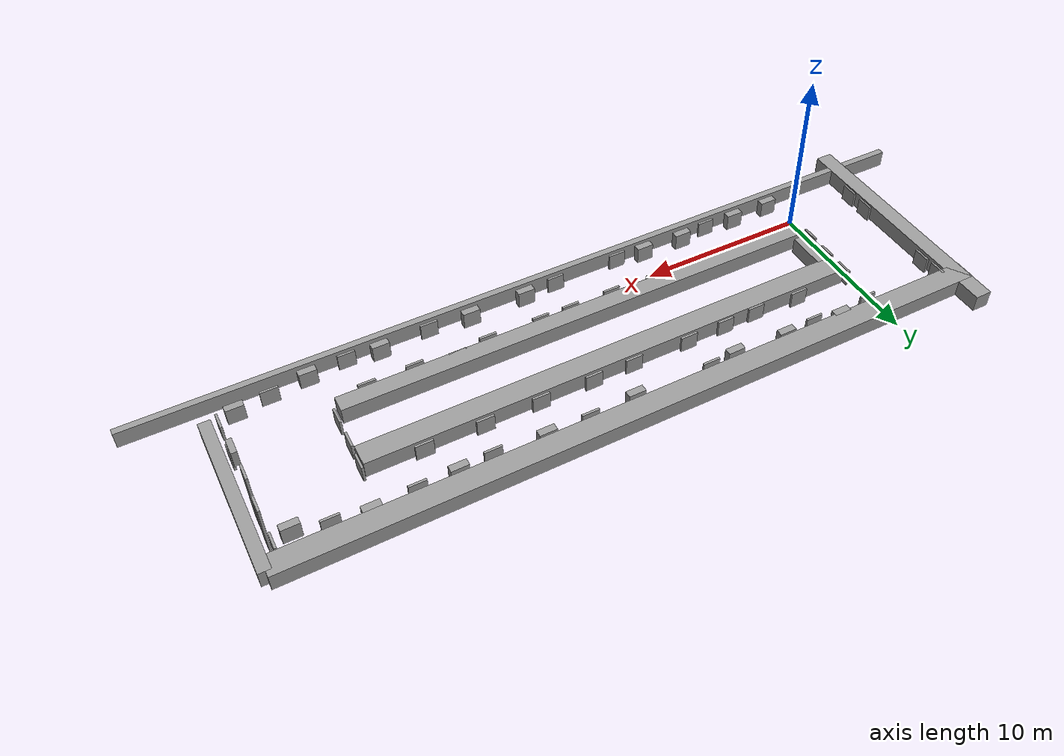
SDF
<sdf version="1.6">
 <world name="default">
  <scene>
   <grid>0</grid>
   <ambient>0.4 0.4 0.4 1</ambient>
   <background>0.7 0.7 0.7 1</background>
   <shadows>1</shadows>
  </scene>
  <light name="sun" type="directional">
   <pose>0 0 10 0 -0 0</pose>
   <diffuse>0.8 0.8 0.8 1</diffuse>
   <specular>0.1 0.1 0.1 1</specular>
   <attenuation>
    <range>1000</range>
    <constant>0.9</constant>
    <linear>0.01</linear>
    <quadratic>0.001</quadratic>
   </attenuation>
   <direction>-0.5 0.5 -1</direction>
  </light>
  <model name="ground">
   <link name="body">
    <collision name="geom">
     <geometry><plane><normal>0 0 1</normal><size>1000 1000</size></plane></geometry>
     <surface><friction><ode><mu>100</mu><mu2>50</mu2></ode></friction></surface>
    </collision>
   </link>
   <static>1</static>
  </model>
  <gravity>0 0 -9.8</gravity>
  <magnetic_field>6e-06 2.3e-05 -4.2e-05</magnetic_field>
  <atmosphere type="adiabatic"/>
  <physics name="default_physics" default="0" type="ode">
   <max_step_size>0.001</max_step_size>
   <real_time_factor>1</real_time_factor>
   <real_time_update_rate>1000</real_time_update_rate>
  </physics>
  <spherical_coordinates>
   <surface_model>EARTH_WGS84</surface_model>
   <latitude_deg>0</latitude_deg>
   <longitude_deg>0</longitude_deg>
   <elevation>0</elevation>
   <heading_deg>0</heading_deg>
  </spherical_coordinates>
  <light name="sun_clone" type="directional">
   <pose>56.9096 13.7226 10 0 -0 0</pose>
   <diffuse>0.8 0.8 0.8 1</diffuse>
   <specular>0.1 0.1 0.1 1</specular>
   <direction>-0.408248 0.408248 -0.816497</direction>
   <attenuation>
    <range>1000</range>
    <constant>0.9</constant>
    <linear>0.01</linear>
    <quadratic>0.001</quadratic>
   </attenuation>
  </light>
  <model name="unit_box">
   <link name="link">
    <inertial>
     <mass>1</mass>
     <inertia>
      <ixx>0.166667</ixx>
      <ixy>0</ixy>
      <ixz>0</ixz>
      <iyy>0.166667</iyy>
      <iyz>0</iyz>
      <izz>0.166667</izz>
     </inertia>
    </inertial>
    <visual name="visual">
     <geometry><box><size>1 14.6124 1</size></box></geometry>
     <material>
      <script><name>Gazebo/Grey</name><uri>file://media/materials/scripts/gazebo.material</uri></script>
      <shader type="pixel"/>
      <ambient>0.3 0.3 0.3 1</ambient>
      <diffuse>0.7 0.7 0.7 1</diffuse>
      <specular>0.01 0.01 0.01 1</specular>
      <emissive>0 0 0 1</emissive>
     </material>
    </visual>
    <collision name="collision">
     <geometry><box><size>1 14.6124 1</size></box></geometry>
     <surface>
      <friction>
       <ode><mu>1</mu><mu2>1</mu2><fdir1>0 0 0</fdir1><slip1>0</slip1><slip2>0</slip2></ode>
       <torsional>
        <coefficient>1</coefficient>
        <patch_radius>0</patch_radius>
        <surface_radius>0</surface_radius>
        <use_patch_radius>1</use_patch_radius>
        <ode><slip>0</slip></ode>
       </torsional>
      </friction>
      <bounce><restitution_coefficient>0</restitution_coefficient><threshold>1e+06</threshold></bounce>
      <contact>
       <collide_without_contact>0</collide_without_contact>
       <collide_without_contact_bitmask>1</collide_without_contact_bitmask>
       <collide_bitmask>1</collide_bitmask>
       <ode>
        <soft_cfm>0</soft_cfm>
        <soft_erp>0.2</soft_erp>
        <kp>1e+13</kp>
        <kd>1</kd>
        <max_vel>0.01</max_vel>
        <min_depth>0</min_depth>
       </ode>
       <bullet>
        <split_impulse>1</split_impulse>
        <split_impulse_penetration_threshold>-0.01</split_impulse_penetration_threshold>
        <soft_cfm>0</soft_cfm>
        <soft_erp>0.2</soft_erp>
        <kp>1e+13</kp>
        <kd>1</kd>
       </bullet>
      </contact>
     </surface>
    </collision>
   </link>
   <static>1</static>
   <pose>-5.00918 3.85436 0.5 0 -0 0</pose>
  </model>
  <model name="unit_box_0">
   <link name="link">
    <inertial>
     <mass>1</mass>
     <inertia>
      <ixx>0.166667</ixx>
      <ixy>0</ixy>
      <ixz>0</ixz>
      <iyy>0.166667</iyy>
      <iyz>0</iyz>
      <izz>0.166667</izz>
     </inertia>
    </inertial>
    <visual name="visual">
     <geometry><box><size>48.7334 0.388398 1</size></box></geometry>
     <material>
      <script><name>Gazebo/Grey</name><uri>file://media/materials/scripts/gazebo.material</uri></script>
      <shader type="pixel"/>
      <ambient>0.3 0.3 0.3 1</ambient>
      <diffuse>0.7 0.7 0.7 1</diffuse>
      <specular>0.01 0.01 0.01 1</specular>
      <emissive>0 0 0 1</emissive>
     </material>
    </visual>
    <collision name="collision">
     <geometry><box><size>48.7334 0.388398 1</size></box></geometry>
     <surface>
      <friction>
       <ode><mu>1</mu><mu2>1</mu2><fdir1>0 0 0</fdir1><slip1>0</slip1><slip2>0</slip2></ode>
       <torsional>
        <coefficient>1</coefficient>
        <patch_radius>0</patch_radius>
        <surface_radius>0</surface_radius>
        <use_patch_radius>1</use_patch_radius>
        <ode><slip>0</slip></ode>
       </torsional>
      </friction>
      <bounce><restitution_coefficient>0</restitution_coefficient><threshold>1e+06</threshold></bounce>
      <contact>
       <collide_without_contact>0</collide_without_contact>
       <collide_without_contact_bitmask>1</collide_without_contact_bitmask>
       <collide_bitmask>1</collide_bitmask>
       <ode>
        <soft_cfm>0</soft_cfm>
        <soft_erp>0.2</soft_erp>
        <kp>1e+13</kp>
        <kd>1</kd>
        <max_vel>0.01</max_vel>
        <min_depth>0</min_depth>
       </ode>
       <bullet>
        <split_impulse>1</split_impulse>
        <split_impulse_penetration_threshold>-0.01</split_impulse_penetration_threshold>
        <soft_cfm>0</soft_cfm>
        <soft_erp>0.2</soft_erp>
        <kp>1e+13</kp>
        <kd>1</kd>
       </bullet>
      </contact>
     </surface>
    </collision>
   </link>
   <static>1</static>
   <pose>15.7619 -2.17322 0.5 0 -0 0</pose>
  </model>
  <model name="unit_box_clone">
   <link name="link">
    <inertial>
     <mass>1</mass>
     <inertia>
      <ixx>0.166667</ixx>
      <ixy>0</ixy>
      <ixz>0</ixz>
      <iyy>0.166667</iyy>
      <iyz>0</iyz>
      <izz>0.166667</izz>
     </inertia>
    </inertial>
    <visual name="visual">
     <geometry><box><size>0.68148 9.92291 1</size></box></geometry>
     <material>
      <script><name>Gazebo/Grey</name><uri>file://media/materials/scripts/gazebo.material</uri></script>
      <shader type="pixel"/>
      <ambient>0.3 0.3 0.3 1</ambient>
      <diffuse>0.7 0.7 0.7 1</diffuse>
      <specular>0.01 0.01 0.01 1</specular>
      <emissive>0 0 0 1</emissive>
     </material>
    </visual>
    <collision name="collision">
     <geometry><box><size>0.68148 9.92291 1</size></box></geometry>
     <surface>
      <friction>
       <ode><mu>1</mu><mu2>1</mu2><fdir1>0 0 0</fdir1><slip1>0</slip1><slip2>0</slip2></ode>
       <torsional>
        <coefficient>1</coefficient>
        <patch_radius>0</patch_radius>
        <surface_radius>0</surface_radius>
        <use_patch_radius>1</use_patch_radius>
        <ode><slip>0</slip></ode>
       </torsional>
      </friction>
      <bounce><restitution_coefficient>0</restitution_coefficient><threshold>1e+06</threshold></bounce>
      <contact>
       <collide_without_contact>0</collide_without_contact>
       <collide_without_contact_bitmask>1</collide_without_contact_bitmask>
       <collide_bitmask>1</collide_bitmask>
       <ode>
        <soft_cfm>0</soft_cfm>
        <soft_erp>0.2</soft_erp>
        <kp>1e+13</kp>
        <kd>1</kd>
        <max_vel>0.01</max_vel>
        <min_depth>0</min_depth>
       </ode>
       <bullet>
        <split_impulse>1</split_impulse>
        <split_impulse_penetration_threshold>-0.01</split_impulse_penetration_threshold>
        <soft_cfm>0</soft_cfm>
        <soft_erp>0.2</soft_erp>
        <kp>1e+13</kp>
        <kd>1</kd>
       </bullet>
      </contact>
     </surface>
    </collision>
   </link>
   <static>1</static>
   <pose>35.8927 4.33216 0.500415 0 -0 0</pose>
  </model>
  <model name="unit_box_0_clone">
   <link name="link">
    <inertial>
     <mass>1</mass>
     <inertia>
      <ixx>0.166667</ixx>
      <ixy>0</ixy>
      <ixz>0</ixz>
      <iyy>0.166667</iyy>
      <iyz>0</iyz>
      <izz>0.166667</izz>
     </inertia>
    </inertial>
    <visual name="visual">
     <geometry><box><size>41.397 1.26672 1</size></box></geometry>
     <material>
      <script><name>Gazebo/Grey</name><uri>file://media/materials/scripts/gazebo.material</uri></script>
      <shader type="pixel"/>
      <ambient>0.3 0.3 0.3 1</ambient>
      <diffuse>0.7 0.7 0.7 1</diffuse>
      <specular>0.01 0.01 0.01 1</specular>
      <emissive>0 0 0 1</emissive>
     </material>
    </visual>
    <collision name="collision">
     <geometry><box><size>41.397 1.26672 1</size></box></geometry>
     <surface>
      <friction>
       <ode><mu>1</mu><mu2>1</mu2><fdir1>0 0 0</fdir1><slip1>0</slip1><slip2>0</slip2></ode>
       <torsional>
        <coefficient>1</coefficient>
        <patch_radius>0</patch_radius>
        <surface_radius>0</surface_radius>
        <use_patch_radius>1</use_patch_radius>
        <ode><slip>0</slip></ode>
       </torsional>
      </friction>
      <bounce><restitution_coefficient>0</restitution_coefficient><threshold>1e+06</threshold></bounce>
      <contact>
       <collide_without_contact>0</collide_without_contact>
       <collide_without_contact_bitmask>1</collide_without_contact_bitmask>
       <collide_bitmask>1</collide_bitmask>
       <ode>
        <soft_cfm>0</soft_cfm>
        <soft_erp>0.2</soft_erp>
        <kp>1e+13</kp>
        <kd>1</kd>
        <max_vel>0.01</max_vel>
        <min_depth>0</min_depth>
       </ode>
       <bullet>
        <split_impulse>1</split_impulse>
        <split_impulse_penetration_threshold>-0.01</split_impulse_penetration_threshold>
        <soft_cfm>0</soft_cfm>
        <soft_erp>0.2</soft_erp>
        <kp>1e+13</kp>
        <kd>1</kd>
       </bullet>
      </contact>
     </surface>
    </collision>
   </link>
   <static>1</static>
   <pose>15.1633 9.04141 0.5 0 -0 0</pose>
  </model>
  <model name="unit_box_1_clone_0_clone">
   <link name="link">
    <inertial>
     <mass>1</mass>
     <inertia>
      <ixx>0.166667</ixx>
      <ixy>0</ixy>
      <ixz>0</ixz>
      <iyy>0.166667</iyy>
      <iyz>0</iyz>
      <izz>0.166667</izz>
     </inertia>
    </inertial>
    <visual name="visual">
     <geometry><box><size>1 0.413614 1</size></box></geometry>
     <material>
      <script><name>Gazebo/Grey</name><uri>file://media/materials/scripts/gazebo.material</uri></script>
      <shader type="pixel"/>
      <ambient>0.3 0.3 0.3 1</ambient>
      <diffuse>0.7 0.7 0.7 1</diffuse>
      <specular>0.01 0.01 0.01 1</specular>
      <emissive>0 0 0 1</emissive>
     </material>
    </visual>
    <collision name="collision">
     <geometry><box><size>1 0.413614 1</size></box></geometry>
     <surface>
      <friction>
       <ode><mu>1</mu><mu2>1</mu2><fdir1>0 0 0</fdir1><slip1>0</slip1><slip2>0</slip2></ode>
       <torsional>
        <coefficient>1</coefficient>
        <patch_radius>0</patch_radius>
        <surface_radius>0</surface_radius>
        <use_patch_radius>1</use_patch_radius>
        <ode><slip>0</slip></ode>
       </torsional>
      </friction>
      <bounce><restitution_coefficient>0</restitution_coefficient><threshold>1e+06</threshold></bounce>
      <contact>
       <collide_without_contact>0</collide_without_contact>
       <collide_without_contact_bitmask>1</collide_without_contact_bitmask>
       <collide_bitmask>1</collide_bitmask>
       <ode>
        <soft_cfm>0</soft_cfm>
        <soft_erp>0.2</soft_erp>
        <kp>1e+13</kp>
        <kd>1</kd>
        <max_vel>0.01</max_vel>
        <min_depth>0</min_depth>
       </ode>
       <bullet>
        <split_impulse>1</split_impulse>
        <split_impulse_penetration_threshold>-0.01</split_impulse_penetration_threshold>
        <soft_cfm>0</soft_cfm>
        <soft_erp>0.2</soft_erp>
        <kp>1e+13</kp>
        <kd>1</kd>
       </bullet>
      </contact>
     </surface>
    </collision>
   </link>
   <static>1</static>
   <pose>2.76595 8.31502 0.500033 1e-05 -0 0</pose>
  </model>
  <model name="unit_box_1_clone_0_clone_0">
   <link name="link">
    <inertial>
     <mass>1</mass>
     <inertia>
      <ixx>0.166667</ixx>
      <ixy>0</ixy>
      <ixz>0</ixz>
      <iyy>0.166667</iyy>
      <iyz>0</iyz>
      <izz>0.166667</izz>
     </inertia>
    </inertial>
    <visual name="visual">
     <geometry><box><size>1 0.413614 1</size></box></geometry>
     <material>
      <script><name>Gazebo/Grey</name><uri>file://media/materials/scripts/gazebo.material</uri></script>
      <shader type="pixel"/>
      <ambient>0.3 0.3 0.3 1</ambient>
      <diffuse>0.7 0.7 0.7 1</diffuse>
      <specular>0.01 0.01 0.01 1</specular>
      <emissive>0 0 0 1</emissive>
     </material>
    </visual>
    <collision name="collision">
     <geometry><box><size>1 0.413614 1</size></box></geometry>
     <surface>
      <friction>
       <ode><mu>1</mu><mu2>1</mu2><fdir1>0 0 0</fdir1><slip1>0</slip1><slip2>0</slip2></ode>
       <torsional>
        <coefficient>1</coefficient>
        <patch_radius>0</patch_radius>
        <surface_radius>0</surface_radius>
        <use_patch_radius>1</use_patch_radius>
        <ode><slip>0</slip></ode>
       </torsional>
      </friction>
      <bounce><restitution_coefficient>0</restitution_coefficient><threshold>1e+06</threshold></bounce>
      <contact>
       <collide_without_contact>0</collide_without_contact>
       <collide_without_contact_bitmask>1</collide_without_contact_bitmask>
       <collide_bitmask>1</collide_bitmask>
       <ode>
        <soft_cfm>0</soft_cfm>
        <soft_erp>0.2</soft_erp>
        <kp>1e+13</kp>
        <kd>1</kd>
        <max_vel>0.01</max_vel>
        <min_depth>0</min_depth>
       </ode>
       <bullet>
        <split_impulse>1</split_impulse>
        <split_impulse_penetration_threshold>-0.01</split_impulse_penetration_threshold>
        <soft_cfm>0</soft_cfm>
        <soft_erp>0.2</soft_erp>
        <kp>1e+13</kp>
        <kd>1</kd>
       </bullet>
      </contact>
     </surface>
    </collision>
   </link>
   <static>1</static>
   <pose>0.76029 -1.57543 0.500034 1e-05 -0 0</pose>
  </model>
  <model name="unit_box_1_clone_0_clone_1">
   <link name="link">
    <inertial>
     <mass>1</mass>
     <inertia>
      <ixx>0.166667</ixx>
      <ixy>0</ixy>
      <ixz>0</ixz>
      <iyy>0.166667</iyy>
      <iyz>0</iyz>
      <izz>0.166667</izz>
     </inertia>
    </inertial>
    <visual name="visual">
     <geometry><box><size>1 0.413614 1</size></box></geometry>
     <material>
      <script><name>Gazebo/Grey</name><uri>file://media/materials/scripts/gazebo.material</uri></script>
      <shader type="pixel"/>
      <ambient>0.3 0.3 0.3 1</ambient>
      <diffuse>0.7 0.7 0.7 1</diffuse>
      <specular>0.01 0.01 0.01 1</specular>
      <emissive>0 0 0 1</emissive>
     </material>
    </visual>
    <collision name="collision">
     <geometry><box><size>1 0.413614 1</size></box></geometry>
     <surface>
      <friction>
       <ode><mu>1</mu><mu2>1</mu2><fdir1>0 0 0</fdir1><slip1>0</slip1><slip2>0</slip2></ode>
       <torsional>
        <coefficient>1</coefficient>
        <patch_radius>0</patch_radius>
        <surface_radius>0</surface_radius>
        <use_patch_radius>1</use_patch_radius>
        <ode><slip>0</slip></ode>
       </torsional>
      </friction>
      <bounce><restitution_coefficient>0</restitution_coefficient><threshold>1e+06</threshold></bounce>
      <contact>
       <collide_without_contact>0</collide_without_contact>
       <collide_without_contact_bitmask>1</collide_without_contact_bitmask>
       <collide_bitmask>1</collide_bitmask>
       <ode>
        <soft_cfm>0</soft_cfm>
        <soft_erp>0.2</soft_erp>
        <kp>1e+13</kp>
        <kd>1</kd>
        <max_vel>0.01</max_vel>
        <min_depth>0</min_depth>
       </ode>
       <bullet>
        <split_impulse>1</split_impulse>
        <split_impulse_penetration_threshold>-0.01</split_impulse_penetration_threshold>
        <soft_cfm>0</soft_cfm>
        <soft_erp>0.2</soft_erp>
        <kp>1e+13</kp>
        <kd>1</kd>
       </bullet>
      </contact>
     </surface>
    </collision>
   </link>
   <static>1</static>
   <pose>3.25411 -1.54906 0.500034 1e-05 -0 0</pose>
  </model>
  <model name="unit_box_1_clone_0_clone_2">
   <link name="link">
    <inertial>
     <mass>1</mass>
     <inertia>
      <ixx>0.166667</ixx>
      <ixy>0</ixy>
      <ixz>0</ixz>
      <iyy>0.166667</iyy>
      <iyz>0</iyz>
      <izz>0.166667</izz>
     </inertia>
    </inertial>
    <visual name="visual">
     <geometry><box><size>1 0.413614 1</size></box></geometry>
     <material>
      <script><name>Gazebo/Grey</name><uri>file://media/materials/scripts/gazebo.material</uri></script>
      <shader type="pixel"/>
      <ambient>0.3 0.3 0.3 1</ambient>
      <diffuse>0.7 0.7 0.7 1</diffuse>
      <specular>0.01 0.01 0.01 1</specular>
      <emissive>0 0 0 1</emissive>
     </material>
    </visual>
    <collision name="collision">
     <geometry><box><size>1 0.413614 1</size></box></geometry>
     <surface>
      <friction>
       <ode><mu>1</mu><mu2>1</mu2><fdir1>0 0 0</fdir1><slip1>0</slip1><slip2>0</slip2></ode>
       <torsional>
        <coefficient>1</coefficient>
        <patch_radius>0</patch_radius>
        <surface_radius>0</surface_radius>
        <use_patch_radius>1</use_patch_radius>
        <ode><slip>0</slip></ode>
       </torsional>
      </friction>
      <bounce><restitution_coefficient>0</restitution_coefficient><threshold>1e+06</threshold></bounce>
      <contact>
       <collide_without_contact>0</collide_without_contact>
       <collide_without_contact_bitmask>1</collide_without_contact_bitmask>
       <collide_bitmask>1</collide_bitmask>
       <ode>
        <soft_cfm>0</soft_cfm>
        <soft_erp>0.2</soft_erp>
        <kp>1e+13</kp>
        <kd>1</kd>
        <max_vel>0.01</max_vel>
        <min_depth>0</min_depth>
       </ode>
       <bullet>
        <split_impulse>1</split_impulse>
        <split_impulse_penetration_threshold>-0.01</split_impulse_penetration_threshold>
        <soft_cfm>0</soft_cfm>
        <soft_erp>0.2</soft_erp>
        <kp>1e+13</kp>
        <kd>1</kd>
       </bullet>
      </contact>
     </surface>
    </collision>
   </link>
   <static>1</static>
   <pose>6.96561 -1.50266 0.500035 1e-05 -0 0</pose>
  </model>
  <model name="unit_box_1_clone_0_clone_3">
   <link name="link">
    <inertial>
     <mass>1</mass>
     <inertia>
      <ixx>0.166667</ixx>
      <ixy>0</ixy>
      <ixz>0</ixz>
      <iyy>0.166667</iyy>
      <iyz>0</iyz>
      <izz>0.166667</izz>
     </inertia>
    </inertial>
    <visual name="visual">
     <geometry><box><size>1 0.413614 1</size></box></geometry>
     <material>
      <script><name>Gazebo/Grey</name><uri>file://media/materials/scripts/gazebo.material</uri></script>
      <shader type="pixel"/>
      <ambient>0.3 0.3 0.3 1</ambient>
      <diffuse>0.7 0.7 0.7 1</diffuse>
      <specular>0.01 0.01 0.01 1</specular>
      <emissive>0 0 0 1</emissive>
     </material>
    </visual>
    <collision name="collision">
     <geometry><box><size>1 0.413614 1</size></box></geometry>
     <surface>
      <friction>
       <ode><mu>1</mu><mu2>1</mu2><fdir1>0 0 0</fdir1><slip1>0</slip1><slip2>0</slip2></ode>
       <torsional>
        <coefficient>1</coefficient>
        <patch_radius>0</patch_radius>
        <surface_radius>0</surface_radius>
        <use_patch_radius>1</use_patch_radius>
        <ode><slip>0</slip></ode>
       </torsional>
      </friction>
      <bounce><restitution_coefficient>0</restitution_coefficient><threshold>1e+06</threshold></bounce>
      <contact>
       <collide_without_contact>0</collide_without_contact>
       <collide_without_contact_bitmask>1</collide_without_contact_bitmask>
       <collide_bitmask>1</collide_bitmask>
       <ode>
        <soft_cfm>0</soft_cfm>
        <soft_erp>0.2</soft_erp>
        <kp>1e+13</kp>
        <kd>1</kd>
        <max_vel>0.01</max_vel>
        <min_depth>0</min_depth>
       </ode>
       <bullet>
        <split_impulse>1</split_impulse>
        <split_impulse_penetration_threshold>-0.01</split_impulse_penetration_threshold>
        <soft_cfm>0</soft_cfm>
        <soft_erp>0.2</soft_erp>
        <kp>1e+13</kp>
        <kd>1</kd>
       </bullet>
      </contact>
     </surface>
    </collision>
   </link>
   <static>1</static>
   <pose>9.54835 -1.57303 0.500034 1e-05 -0 0</pose>
  </model>
  <model name="unit_box_1_clone_0_clone_4">
   <link name="link">
    <inertial>
     <mass>1</mass>
     <inertia>
      <ixx>0.166667</ixx>
      <ixy>0</ixy>
      <ixz>0</ixz>
      <iyy>0.166667</iyy>
      <iyz>0</iyz>
      <izz>0.166667</izz>
     </inertia>
    </inertial>
    <visual name="visual">
     <geometry><box><size>1 0.413614 1</size></box></geometry>
     <material>
      <script><name>Gazebo/Grey</name><uri>file://media/materials/scripts/gazebo.material</uri></script>
      <shader type="pixel"/>
      <ambient>0.3 0.3 0.3 1</ambient>
      <diffuse>0.7 0.7 0.7 1</diffuse>
      <specular>0.01 0.01 0.01 1</specular>
      <emissive>0 0 0 1</emissive>
     </material>
    </visual>
    <collision name="collision">
     <geometry><box><size>1 0.413614 1</size></box></geometry>
     <surface>
      <friction>
       <ode><mu>1</mu><mu2>1</mu2><fdir1>0 0 0</fdir1><slip1>0</slip1><slip2>0</slip2></ode>
       <torsional>
        <coefficient>1</coefficient>
        <patch_radius>0</patch_radius>
        <surface_radius>0</surface_radius>
        <use_patch_radius>1</use_patch_radius>
        <ode><slip>0</slip></ode>
       </torsional>
      </friction>
      <bounce><restitution_coefficient>0</restitution_coefficient><threshold>1e+06</threshold></bounce>
      <contact>
       <collide_without_contact>0</collide_without_contact>
       <collide_without_contact_bitmask>1</collide_without_contact_bitmask>
       <collide_bitmask>1</collide_bitmask>
       <ode>
        <soft_cfm>0</soft_cfm>
        <soft_erp>0.2</soft_erp>
        <kp>1e+13</kp>
        <kd>1</kd>
        <max_vel>0.01</max_vel>
        <min_depth>0</min_depth>
       </ode>
       <bullet>
        <split_impulse>1</split_impulse>
        <split_impulse_penetration_threshold>-0.01</split_impulse_penetration_threshold>
        <soft_cfm>0</soft_cfm>
        <soft_erp>0.2</soft_erp>
        <kp>1e+13</kp>
        <kd>1</kd>
       </bullet>
      </contact>
     </surface>
    </collision>
   </link>
   <static>1</static>
   <pose>17.3571 -1.53233 0.500035 1e-05 -0 0</pose>
  </model>
  <model name="unit_box_1_clone_0_clone_5">
   <link name="link">
    <inertial>
     <mass>1</mass>
     <inertia>
      <ixx>0.166667</ixx>
      <ixy>0</ixy>
      <ixz>0</ixz>
      <iyy>0.166667</iyy>
      <iyz>0</iyz>
      <izz>0.166667</izz>
     </inertia>
    </inertial>
    <visual name="visual">
     <geometry><box><size>1 0.413614 1</size></box></geometry>
     <material>
      <script><name>Gazebo/Grey</name><uri>file://media/materials/scripts/gazebo.material</uri></script>
      <shader type="pixel"/>
      <ambient>0.3 0.3 0.3 1</ambient>
      <diffuse>0.7 0.7 0.7 1</diffuse>
      <specular>0.01 0.01 0.01 1</specular>
      <emissive>0 0 0 1</emissive>
     </material>
    </visual>
    <collision name="collision">
     <geometry><box><size>1 0.413614 1</size></box></geometry>
     <surface>
      <friction>
       <ode><mu>1</mu><mu2>1</mu2><fdir1>0 0 0</fdir1><slip1>0</slip1><slip2>0</slip2></ode>
       <torsional>
        <coefficient>1</coefficient>
        <patch_radius>0</patch_radius>
        <surface_radius>0</surface_radius>
        <use_patch_radius>1</use_patch_radius>
        <ode><slip>0</slip></ode>
       </torsional>
      </friction>
      <bounce><restitution_coefficient>0</restitution_coefficient><threshold>1e+06</threshold></bounce>
      <contact>
       <collide_without_contact>0</collide_without_contact>
       <collide_without_contact_bitmask>1</collide_without_contact_bitmask>
       <collide_bitmask>1</collide_bitmask>
       <ode>
        <soft_cfm>0</soft_cfm>
        <soft_erp>0.2</soft_erp>
        <kp>1e+13</kp>
        <kd>1</kd>
        <max_vel>0.01</max_vel>
        <min_depth>0</min_depth>
       </ode>
       <bullet>
        <split_impulse>1</split_impulse>
        <split_impulse_penetration_threshold>-0.01</split_impulse_penetration_threshold>
        <soft_cfm>0</soft_cfm>
        <soft_erp>0.2</soft_erp>
        <kp>1e+13</kp>
        <kd>1</kd>
       </bullet>
      </contact>
     </surface>
    </collision>
   </link>
   <static>1</static>
   <pose>6.3125 8.09635 0.500032 1e-05 -0 0</pose>
  </model>
  <model name="unit_box_1_clone_0_clone_6">
   <link name="link">
    <inertial>
     <mass>1</mass>
     <inertia>
      <ixx>0.166667</ixx>
      <ixy>0</ixy>
      <ixz>0</ixz>
      <iyy>0.166667</iyy>
      <iyz>0</iyz>
      <izz>0.166667</izz>
     </inertia>
    </inertial>
    <visual name="visual">
     <geometry><box><size>1 0.413614 1</size></box></geometry>
     <material>
      <script><name>Gazebo/Grey</name><uri>file://media/materials/scripts/gazebo.material</uri></script>
      <shader type="pixel"/>
      <ambient>0.3 0.3 0.3 1</ambient>
      <diffuse>0.7 0.7 0.7 1</diffuse>
      <specular>0.01 0.01 0.01 1</specular>
      <emissive>0 0 0 1</emissive>
     </material>
    </visual>
    <collision name="collision">
     <geometry><box><size>1 0.413614 1</size></box></geometry>
     <surface>
      <friction>
       <ode><mu>1</mu><mu2>1</mu2><fdir1>0 0 0</fdir1><slip1>0</slip1><slip2>0</slip2></ode>
       <torsional>
        <coefficient>1</coefficient>
        <patch_radius>0</patch_radius>
        <surface_radius>0</surface_radius>
        <use_patch_radius>1</use_patch_radius>
        <ode><slip>0</slip></ode>
       </torsional>
      </friction>
      <bounce><restitution_coefficient>0</restitution_coefficient><threshold>1e+06</threshold></bounce>
      <contact>
       <collide_without_contact>0</collide_without_contact>
       <collide_without_contact_bitmask>1</collide_without_contact_bitmask>
       <collide_bitmask>1</collide_bitmask>
       <ode>
        <soft_cfm>0</soft_cfm>
        <soft_erp>0.2</soft_erp>
        <kp>1e+13</kp>
        <kd>1</kd>
        <max_vel>0.01</max_vel>
        <min_depth>0</min_depth>
       </ode>
       <bullet>
        <split_impulse>1</split_impulse>
        <split_impulse_penetration_threshold>-0.01</split_impulse_penetration_threshold>
        <soft_cfm>0</soft_cfm>
        <soft_erp>0.2</soft_erp>
        <kp>1e+13</kp>
        <kd>1</kd>
       </bullet>
      </contact>
     </surface>
    </collision>
   </link>
   <static>1</static>
   <pose>9.55963 7.943 0.50003 1e-05 -0 0</pose>
  </model>
  <model name="unit_box_1_clone_0_clone_7">
   <link name="link">
    <inertial>
     <mass>1</mass>
     <inertia>
      <ixx>0.166667</ixx>
      <ixy>0</ixy>
      <ixz>0</ixz>
      <iyy>0.166667</iyy>
      <iyz>0</iyz>
      <izz>0.166667</izz>
     </inertia>
    </inertial>
    <visual name="visual">
     <geometry><box><size>1 0.413614 1</size></box></geometry>
     <material>
      <script><name>Gazebo/Grey</name><uri>file://media/materials/scripts/gazebo.material</uri></script>
      <shader type="pixel"/>
      <ambient>0.3 0.3 0.3 1</ambient>
      <diffuse>0.7 0.7 0.7 1</diffuse>
      <specular>0.01 0.01 0.01 1</specular>
      <emissive>0 0 0 1</emissive>
     </material>
    </visual>
    <collision name="collision">
     <geometry><box><size>1 0.413614 1</size></box></geometry>
     <surface>
      <friction>
       <ode><mu>1</mu><mu2>1</mu2><fdir1>0 0 0</fdir1><slip1>0</slip1><slip2>0</slip2></ode>
       <torsional>
        <coefficient>1</coefficient>
        <patch_radius>0</patch_radius>
        <surface_radius>0</surface_radius>
        <use_patch_radius>1</use_patch_radius>
        <ode><slip>0</slip></ode>
       </torsional>
      </friction>
      <bounce><restitution_coefficient>0</restitution_coefficient><threshold>1e+06</threshold></bounce>
      <contact>
       <collide_without_contact>0</collide_without_contact>
       <collide_without_contact_bitmask>1</collide_without_contact_bitmask>
       <collide_bitmask>1</collide_bitmask>
       <ode>
        <soft_cfm>0</soft_cfm>
        <soft_erp>0.2</soft_erp>
        <kp>1e+13</kp>
        <kd>1</kd>
        <max_vel>0.01</max_vel>
        <min_depth>0</min_depth>
       </ode>
       <bullet>
        <split_impulse>1</split_impulse>
        <split_impulse_penetration_threshold>-0.01</split_impulse_penetration_threshold>
        <soft_cfm>0</soft_cfm>
        <soft_erp>0.2</soft_erp>
        <kp>1e+13</kp>
        <kd>1</kd>
       </bullet>
      </contact>
     </surface>
    </collision>
   </link>
   <static>1</static>
   <pose>15.7661 7.99336 0.50003 1e-05 -0 0</pose>
  </model>
  <model name="unit_box_1_clone_0_clone_8">
   <link name="link">
    <inertial>
     <mass>1</mass>
     <inertia>
      <ixx>0.166667</ixx>
      <ixy>0</ixy>
      <ixz>0</ixz>
      <iyy>0.166667</iyy>
      <iyz>0</iyz>
      <izz>0.166667</izz>
     </inertia>
    </inertial>
    <visual name="visual">
     <geometry><box><size>1 0.413614 1</size></box></geometry>
     <material>
      <script><name>Gazebo/Grey</name><uri>file://media/materials/scripts/gazebo.material</uri></script>
      <shader type="pixel"/>
      <ambient>0.3 0.3 0.3 1</ambient>
      <diffuse>0.7 0.7 0.7 1</diffuse>
      <specular>0.01 0.01 0.01 1</specular>
      <emissive>0 0 0 1</emissive>
     </material>
    </visual>
    <collision name="collision">
     <geometry><box><size>1 0.413614 1</size></box></geometry>
     <surface>
      <friction>
       <ode><mu>1</mu><mu2>1</mu2><fdir1>0 0 0</fdir1><slip1>0</slip1><slip2>0</slip2></ode>
       <torsional>
        <coefficient>1</coefficient>
        <patch_radius>0</patch_radius>
        <surface_radius>0</surface_radius>
        <use_patch_radius>1</use_patch_radius>
        <ode><slip>0</slip></ode>
       </torsional>
      </friction>
      <bounce><restitution_coefficient>0</restitution_coefficient><threshold>1e+06</threshold></bounce>
      <contact>
       <collide_without_contact>0</collide_without_contact>
       <collide_without_contact_bitmask>1</collide_without_contact_bitmask>
       <collide_bitmask>1</collide_bitmask>
       <ode>
        <soft_cfm>0</soft_cfm>
        <soft_erp>0.2</soft_erp>
        <kp>1e+13</kp>
        <kd>1</kd>
        <max_vel>0.01</max_vel>
        <min_depth>0</min_depth>
       </ode>
       <bullet>
        <split_impulse>1</split_impulse>
        <split_impulse_penetration_threshold>-0.01</split_impulse_penetration_threshold>
        <soft_cfm>0</soft_cfm>
        <soft_erp>0.2</soft_erp>
        <kp>1e+13</kp>
        <kd>1</kd>
       </bullet>
      </contact>
     </surface>
    </collision>
   </link>
   <static>1</static>
   <pose>20.9877 8.09078 0.500032 1e-05 -0 0</pose>
  </model>
  <model name="unit_box_1_clone_0_clone_9">
   <link name="link">
    <inertial>
     <mass>1</mass>
     <inertia>
      <ixx>0.166667</ixx>
      <ixy>0</ixy>
      <ixz>0</ixz>
      <iyy>0.166667</iyy>
      <iyz>0</iyz>
      <izz>0.166667</izz>
     </inertia>
    </inertial>
    <visual name="visual">
     <geometry><box><size>1 0.413614 1</size></box></geometry>
     <material>
      <script><name>Gazebo/Grey</name><uri>file://media/materials/scripts/gazebo.material</uri></script>
      <shader type="pixel"/>
      <ambient>0.3 0.3 0.3 1</ambient>
      <diffuse>0.7 0.7 0.7 1</diffuse>
      <specular>0.01 0.01 0.01 1</specular>
      <emissive>0 0 0 1</emissive>
     </material>
    </visual>
    <collision name="collision">
     <geometry><box><size>1 0.413614 1</size></box></geometry>
     <surface>
      <friction>
       <ode><mu>1</mu><mu2>1</mu2><fdir1>0 0 0</fdir1><slip1>0</slip1><slip2>0</slip2></ode>
       <torsional>
        <coefficient>1</coefficient>
        <patch_radius>0</patch_radius>
        <surface_radius>0</surface_radius>
        <use_patch_radius>1</use_patch_radius>
        <ode><slip>0</slip></ode>
       </torsional>
      </friction>
      <bounce><restitution_coefficient>0</restitution_coefficient><threshold>1e+06</threshold></bounce>
      <contact>
       <collide_without_contact>0</collide_without_contact>
       <collide_without_contact_bitmask>1</collide_without_contact_bitmask>
       <collide_bitmask>1</collide_bitmask>
       <ode>
        <soft_cfm>0</soft_cfm>
        <soft_erp>0.2</soft_erp>
        <kp>1e+13</kp>
        <kd>1</kd>
        <max_vel>0.01</max_vel>
        <min_depth>0</min_depth>
       </ode>
       <bullet>
        <split_impulse>1</split_impulse>
        <split_impulse_penetration_threshold>-0.01</split_impulse_penetration_threshold>
        <soft_cfm>0</soft_cfm>
        <soft_erp>0.2</soft_erp>
        <kp>1e+13</kp>
        <kd>1</kd>
       </bullet>
      </contact>
     </surface>
    </collision>
   </link>
   <static>1</static>
   <pose>25.7785 8.00947 0.500039 1e-05 -0 0</pose>
  </model>
  <model name="unit_box_1_clone_0_clone_10">
   <link name="link">
    <inertial>
     <mass>1</mass>
     <inertia>
      <ixx>0.166667</ixx>
      <ixy>0</ixy>
      <ixz>0</ixz>
      <iyy>0.166667</iyy>
      <iyz>0</iyz>
      <izz>0.166667</izz>
     </inertia>
    </inertial>
    <visual name="visual">
     <geometry><box><size>1 0.413614 1</size></box></geometry>
     <material>
      <script><name>Gazebo/Grey</name><uri>file://media/materials/scripts/gazebo.material</uri></script>
      <shader type="pixel"/>
      <ambient>0.3 0.3 0.3 1</ambient>
      <diffuse>0.7 0.7 0.7 1</diffuse>
      <specular>0.01 0.01 0.01 1</specular>
      <emissive>0 0 0 1</emissive>
     </material>
    </visual>
    <collision name="collision">
     <geometry><box><size>1 0.413614 1</size></box></geometry>
     <surface>
      <friction>
       <ode><mu>1</mu><mu2>1</mu2><fdir1>0 0 0</fdir1><slip1>0</slip1><slip2>0</slip2></ode>
       <torsional>
        <coefficient>1</coefficient>
        <patch_radius>0</patch_radius>
        <surface_radius>0</surface_radius>
        <use_patch_radius>1</use_patch_radius>
        <ode><slip>0</slip></ode>
       </torsional>
      </friction>
      <bounce><restitution_coefficient>0</restitution_coefficient><threshold>1e+06</threshold></bounce>
      <contact>
       <collide_without_contact>0</collide_without_contact>
       <collide_without_contact_bitmask>1</collide_without_contact_bitmask>
       <collide_bitmask>1</collide_bitmask>
       <ode>
        <soft_cfm>0</soft_cfm>
        <soft_erp>0.2</soft_erp>
        <kp>1e+13</kp>
        <kd>1</kd>
        <max_vel>0.01</max_vel>
        <min_depth>0</min_depth>
       </ode>
       <bullet>
        <split_impulse>1</split_impulse>
        <split_impulse_penetration_threshold>-0.01</split_impulse_penetration_threshold>
        <soft_cfm>0</soft_cfm>
        <soft_erp>0.2</soft_erp>
        <kp>1e+13</kp>
        <kd>1</kd>
       </bullet>
      </contact>
     </surface>
    </collision>
   </link>
   <static>1</static>
   <pose>30.3719 8.20697 0.500039 1e-05 -0 0</pose>
  </model>
  <model name="unit_box_1_clone_0_clone_11">
   <link name="link">
    <inertial>
     <mass>1</mass>
     <inertia>
      <ixx>0.166667</ixx>
      <ixy>0</ixy>
      <ixz>0</ixz>
      <iyy>0.166667</iyy>
      <iyz>0</iyz>
      <izz>0.166667</izz>
     </inertia>
    </inertial>
    <visual name="visual">
     <geometry><box><size>1 0.413614 1</size></box></geometry>
     <material>
      <script><name>Gazebo/Grey</name><uri>file://media/materials/scripts/gazebo.material</uri></script>
      <shader type="pixel"/>
      <ambient>0.3 0.3 0.3 1</ambient>
      <diffuse>0.7 0.7 0.7 1</diffuse>
      <specular>0.01 0.01 0.01 1</specular>
      <emissive>0 0 0 1</emissive>
     </material>
    </visual>
    <collision name="collision">
     <geometry><box><size>1 0.413614 1</size></box></geometry>
     <surface>
      <friction>
       <ode><mu>1</mu><mu2>1</mu2><fdir1>0 0 0</fdir1><slip1>0</slip1><slip2>0</slip2></ode>
       <torsional>
        <coefficient>1</coefficient>
        <patch_radius>0</patch_radius>
        <surface_radius>0</surface_radius>
        <use_patch_radius>1</use_patch_radius>
        <ode><slip>0</slip></ode>
       </torsional>
      </friction>
      <bounce><restitution_coefficient>0</restitution_coefficient><threshold>1e+06</threshold></bounce>
      <contact>
       <collide_without_contact>0</collide_without_contact>
       <collide_without_contact_bitmask>1</collide_without_contact_bitmask>
       <collide_bitmask>1</collide_bitmask>
       <ode>
        <soft_cfm>0</soft_cfm>
        <soft_erp>0.2</soft_erp>
        <kp>1e+13</kp>
        <kd>1</kd>
        <max_vel>0.01</max_vel>
        <min_depth>0</min_depth>
       </ode>
       <bullet>
        <split_impulse>1</split_impulse>
        <split_impulse_penetration_threshold>-0.01</split_impulse_penetration_threshold>
        <soft_cfm>0</soft_cfm>
        <soft_erp>0.2</soft_erp>
        <kp>1e+13</kp>
        <kd>1</kd>
       </bullet>
      </contact>
     </surface>
    </collision>
   </link>
   <static>1</static>
   <pose>20.7603 -1.50473 0.500033 1e-05 -0 0</pose>
  </model>
  <model name="unit_box_1_clone_0_clone_12">
   <link name="link">
    <inertial>
     <mass>1</mass>
     <inertia>
      <ixx>0.166667</ixx>
      <ixy>0</ixy>
      <ixz>0</ixz>
      <iyy>0.166667</iyy>
      <iyz>0</iyz>
      <izz>0.166667</izz>
     </inertia>
    </inertial>
    <visual name="visual">
     <geometry><box><size>1 0.413614 1</size></box></geometry>
     <material>
      <script><name>Gazebo/Grey</name><uri>file://media/materials/scripts/gazebo.material</uri></script>
      <shader type="pixel"/>
      <ambient>0.3 0.3 0.3 1</ambient>
      <diffuse>0.7 0.7 0.7 1</diffuse>
      <specular>0.01 0.01 0.01 1</specular>
      <emissive>0 0 0 1</emissive>
     </material>
    </visual>
    <collision name="collision">
     <geometry><box><size>1 0.413614 1</size></box></geometry>
     <surface>
      <friction>
       <ode><mu>1</mu><mu2>1</mu2><fdir1>0 0 0</fdir1><slip1>0</slip1><slip2>0</slip2></ode>
       <torsional>
        <coefficient>1</coefficient>
        <patch_radius>0</patch_radius>
        <surface_radius>0</surface_radius>
        <use_patch_radius>1</use_patch_radius>
        <ode><slip>0</slip></ode>
       </torsional>
      </friction>
      <bounce><restitution_coefficient>0</restitution_coefficient><threshold>1e+06</threshold></bounce>
      <contact>
       <collide_without_contact>0</collide_without_contact>
       <collide_without_contact_bitmask>1</collide_without_contact_bitmask>
       <collide_bitmask>1</collide_bitmask>
       <ode>
        <soft_cfm>0</soft_cfm>
        <soft_erp>0.2</soft_erp>
        <kp>1e+13</kp>
        <kd>1</kd>
        <max_vel>0.01</max_vel>
        <min_depth>0</min_depth>
       </ode>
       <bullet>
        <split_impulse>1</split_impulse>
        <split_impulse_penetration_threshold>-0.01</split_impulse_penetration_threshold>
        <soft_cfm>0</soft_cfm>
        <soft_erp>0.2</soft_erp>
        <kp>1e+13</kp>
        <kd>1</kd>
       </bullet>
      </contact>
     </surface>
    </collision>
   </link>
   <static>1</static>
   <pose>26.1096 -1.52016 0.500033 1e-05 -0 0</pose>
  </model>
  <model name="unit_box_1_clone_0_clone_13">
   <link name="link">
    <inertial>
     <mass>1</mass>
     <inertia>
      <ixx>0.166667</ixx>
      <ixy>0</ixy>
      <ixz>0</ixz>
      <iyy>0.166667</iyy>
      <iyz>0</iyz>
      <izz>0.166667</izz>
     </inertia>
    </inertial>
    <visual name="visual">
     <geometry><box><size>1 0.413614 1</size></box></geometry>
     <material>
      <script><name>Gazebo/Grey</name><uri>file://media/materials/scripts/gazebo.material</uri></script>
      <shader type="pixel"/>
      <ambient>0.3 0.3 0.3 1</ambient>
      <diffuse>0.7 0.7 0.7 1</diffuse>
      <specular>0.01 0.01 0.01 1</specular>
      <emissive>0 0 0 1</emissive>
     </material>
    </visual>
    <collision name="collision">
     <geometry><box><size>1 0.413614 1</size></box></geometry>
     <surface>
      <friction>
       <ode><mu>1</mu><mu2>1</mu2><fdir1>0 0 0</fdir1><slip1>0</slip1><slip2>0</slip2></ode>
       <torsional>
        <coefficient>1</coefficient>
        <patch_radius>0</patch_radius>
        <surface_radius>0</surface_radius>
        <use_patch_radius>1</use_patch_radius>
        <ode><slip>0</slip></ode>
       </torsional>
      </friction>
      <bounce><restitution_coefficient>0</restitution_coefficient><threshold>1e+06</threshold></bounce>
      <contact>
       <collide_without_contact>0</collide_without_contact>
       <collide_without_contact_bitmask>1</collide_without_contact_bitmask>
       <collide_bitmask>1</collide_bitmask>
       <ode>
        <soft_cfm>0</soft_cfm>
        <soft_erp>0.2</soft_erp>
        <kp>1e+13</kp>
        <kd>1</kd>
        <max_vel>0.01</max_vel>
        <min_depth>0</min_depth>
       </ode>
       <bullet>
        <split_impulse>1</split_impulse>
        <split_impulse_penetration_threshold>-0.01</split_impulse_penetration_threshold>
        <soft_cfm>0</soft_cfm>
        <soft_erp>0.2</soft_erp>
        <kp>1e+13</kp>
        <kd>1</kd>
       </bullet>
      </contact>
     </surface>
    </collision>
   </link>
   <static>1</static>
   <pose>30.197 -1.52136 0.500034 1e-05 -0 0</pose>
  </model>
  <model name="unit_box_1_clone_0_clone_14">
   <link name="link">
    <inertial>
     <mass>1</mass>
     <inertia>
      <ixx>0.166667</ixx>
      <ixy>0</ixy>
      <ixz>0</ixz>
      <iyy>0.166667</iyy>
      <iyz>0</iyz>
      <izz>0.166667</izz>
     </inertia>
    </inertial>
    <visual name="visual">
     <geometry><box><size>1 0.413614 1</size></box></geometry>
     <material>
      <script><name>Gazebo/Grey</name><uri>file://media/materials/scripts/gazebo.material</uri></script>
      <shader type="pixel"/>
      <ambient>0.3 0.3 0.3 1</ambient>
      <diffuse>0.7 0.7 0.7 1</diffuse>
      <specular>0.01 0.01 0.01 1</specular>
      <emissive>0 0 0 1</emissive>
     </material>
    </visual>
    <collision name="collision">
     <geometry><box><size>1 0.413614 1</size></box></geometry>
     <surface>
      <friction>
       <ode><mu>1</mu><mu2>1</mu2><fdir1>0 0 0</fdir1><slip1>0</slip1><slip2>0</slip2></ode>
       <torsional>
        <coefficient>1</coefficient>
        <patch_radius>0</patch_radius>
        <surface_radius>0</surface_radius>
        <use_patch_radius>1</use_patch_radius>
        <ode><slip>0</slip></ode>
       </torsional>
      </friction>
      <bounce><restitution_coefficient>0</restitution_coefficient><threshold>1e+06</threshold></bounce>
      <contact>
       <collide_without_contact>0</collide_without_contact>
       <collide_without_contact_bitmask>1</collide_without_contact_bitmask>
       <collide_bitmask>1</collide_bitmask>
       <ode>
        <soft_cfm>0</soft_cfm>
        <soft_erp>0.2</soft_erp>
        <kp>1e+13</kp>
        <kd>1</kd>
        <max_vel>0.01</max_vel>
        <min_depth>0</min_depth>
       </ode>
       <bullet>
        <split_impulse>1</split_impulse>
        <split_impulse_penetration_threshold>-0.01</split_impulse_penetration_threshold>
        <soft_cfm>0</soft_cfm>
        <soft_erp>0.2</soft_erp>
        <kp>1e+13</kp>
        <kd>1</kd>
       </bullet>
      </contact>
     </surface>
    </collision>
   </link>
   <static>1</static>
   <pose>34.1216 7.35234 0.500025 1e-05 -0 0</pose>
  </model>
  <model name="unit_box_1_clone_0_clone_15">
   <link name="link">
    <inertial>
     <mass>1</mass>
     <inertia>
      <ixx>0.166667</ixx>
      <ixy>0</ixy>
      <ixz>0</ixz>
      <iyy>0.166667</iyy>
      <iyz>0</iyz>
      <izz>0.166667</izz>
     </inertia>
    </inertial>
    <visual name="visual">
     <geometry><box><size>1 0.413614 1</size></box></geometry>
     <material>
      <script><name>Gazebo/Grey</name><uri>file://media/materials/scripts/gazebo.material</uri></script>
      <shader type="pixel"/>
      <ambient>0.3 0.3 0.3 1</ambient>
      <diffuse>0.7 0.7 0.7 1</diffuse>
      <specular>0.01 0.01 0.01 1</specular>
      <emissive>0 0 0 1</emissive>
     </material>
    </visual>
    <collision name="collision">
     <geometry><box><size>1 0.413614 1</size></box></geometry>
     <surface>
      <friction>
       <ode><mu>1</mu><mu2>1</mu2><fdir1>0 0 0</fdir1><slip1>0</slip1><slip2>0</slip2></ode>
       <torsional>
        <coefficient>1</coefficient>
        <patch_radius>0</patch_radius>
        <surface_radius>0</surface_radius>
        <use_patch_radius>1</use_patch_radius>
        <ode><slip>0</slip></ode>
       </torsional>
      </friction>
      <bounce><restitution_coefficient>0</restitution_coefficient><threshold>1e+06</threshold></bounce>
      <contact>
       <collide_without_contact>0</collide_without_contact>
       <collide_without_contact_bitmask>1</collide_without_contact_bitmask>
       <collide_bitmask>1</collide_bitmask>
       <ode>
        <soft_cfm>0</soft_cfm>
        <soft_erp>0.2</soft_erp>
        <kp>1e+13</kp>
        <kd>1</kd>
        <max_vel>0.01</max_vel>
        <min_depth>0</min_depth>
       </ode>
       <bullet>
        <split_impulse>1</split_impulse>
        <split_impulse_penetration_threshold>-0.01</split_impulse_penetration_threshold>
        <soft_cfm>0</soft_cfm>
        <soft_erp>0.2</soft_erp>
        <kp>1e+13</kp>
        <kd>1</kd>
       </bullet>
      </contact>
     </surface>
    </collision>
   </link>
   <static>1</static>
   <pose>34.2763 -0.955923 0.500039 1e-05 -0 0</pose>
  </model>
  <model name="unit_box_1_clone_0_clone_16_clone">
   <link name="link">
    <inertial>
     <mass>1</mass>
     <inertia>
      <ixx>0.166667</ixx>
      <ixy>0</ixy>
      <ixz>0</ixz>
      <iyy>0.166667</iyy>
      <iyz>0</iyz>
      <izz>0.166667</izz>
     </inertia>
    </inertial>
    <visual name="visual">
     <geometry><box><size>1 0.12971 1</size></box></geometry>
     <material>
      <script><name>Gazebo/Grey</name><uri>file://media/materials/scripts/gazebo.material</uri></script>
      <shader type="pixel"/>
      <ambient>0.3 0.3 0.3 1</ambient>
      <diffuse>0.7 0.7 0.7 1</diffuse>
      <specular>0.01 0.01 0.01 1</specular>
      <emissive>0 0 0 1</emissive>
     </material>
    </visual>
    <collision name="collision">
     <geometry><box><size>1 0.12971 1</size></box></geometry>
     <surface>
      <friction>
       <ode><mu>1</mu><mu2>1</mu2><fdir1>0 0 0</fdir1><slip1>0</slip1><slip2>0</slip2></ode>
       <torsional>
        <coefficient>1</coefficient>
        <patch_radius>0</patch_radius>
        <surface_radius>0</surface_radius>
        <use_patch_radius>1</use_patch_radius>
        <ode><slip>0</slip></ode>
       </torsional>
      </friction>
      <bounce><restitution_coefficient>0</restitution_coefficient><threshold>1e+06</threshold></bounce>
      <contact>
       <collide_without_contact>0</collide_without_contact>
       <collide_without_contact_bitmask>1</collide_without_contact_bitmask>
       <collide_bitmask>1</collide_bitmask>
       <ode>
        <soft_cfm>0</soft_cfm>
        <soft_erp>0.2</soft_erp>
        <kp>1e+13</kp>
        <kd>1</kd>
        <max_vel>0.01</max_vel>
        <min_depth>0</min_depth>
       </ode>
       <bullet>
        <split_impulse>1</split_impulse>
        <split_impulse_penetration_threshold>-0.01</split_impulse_penetration_threshold>
        <soft_cfm>0</soft_cfm>
        <soft_erp>0.2</soft_erp>
        <kp>1e+13</kp>
        <kd>1</kd>
       </bullet>
      </contact>
     </surface>
    </collision>
   </link>
   <static>1</static>
   <pose>5.17154 -1.66149 0.500002 1e-05 -0 0</pose>
  </model>
  <model name="unit_box_1_clone_0_clone_16_clone_0">
   <link name="link">
    <inertial>
     <mass>1</mass>
     <inertia>
      <ixx>0.166667</ixx>
      <ixy>0</ixy>
      <ixz>0</ixz>
      <iyy>0.166667</iyy>
      <iyz>0</iyz>
      <izz>0.166667</izz>
     </inertia>
    </inertial>
    <visual name="visual">
     <geometry><box><size>1 0.12971 1</size></box></geometry>
     <material>
      <script><name>Gazebo/Grey</name><uri>file://media/materials/scripts/gazebo.material</uri></script>
      <shader type="pixel"/>
      <ambient>0.3 0.3 0.3 1</ambient>
      <diffuse>0.7 0.7 0.7 1</diffuse>
      <specular>0.01 0.01 0.01 1</specular>
      <emissive>0 0 0 1</emissive>
     </material>
    </visual>
    <collision name="collision">
     <geometry><box><size>1 0.12971 1</size></box></geometry>
     <surface>
      <friction>
       <ode><mu>1</mu><mu2>1</mu2><fdir1>0 0 0</fdir1><slip1>0</slip1><slip2>0</slip2></ode>
       <torsional>
        <coefficient>1</coefficient>
        <patch_radius>0</patch_radius>
        <surface_radius>0</surface_radius>
        <use_patch_radius>1</use_patch_radius>
        <ode><slip>0</slip></ode>
       </torsional>
      </friction>
      <bounce><restitution_coefficient>0</restitution_coefficient><threshold>1e+06</threshold></bounce>
      <contact>
       <collide_without_contact>0</collide_without_contact>
       <collide_without_contact_bitmask>1</collide_without_contact_bitmask>
       <collide_bitmask>1</collide_bitmask>
       <ode>
        <soft_cfm>0</soft_cfm>
        <soft_erp>0.2</soft_erp>
        <kp>1e+13</kp>
        <kd>1</kd>
        <max_vel>0.01</max_vel>
        <min_depth>0</min_depth>
       </ode>
       <bullet>
        <split_impulse>1</split_impulse>
        <split_impulse_penetration_threshold>-0.01</split_impulse_penetration_threshold>
        <soft_cfm>0</soft_cfm>
        <soft_erp>0.2</soft_erp>
        <kp>1e+13</kp>
        <kd>1</kd>
       </bullet>
      </contact>
     </surface>
    </collision>
   </link>
   <static>1</static>
   <pose>11.3045 -1.70035 0.500002 1e-05 -0 0</pose>
  </model>
  <model name="unit_box_1_clone_0_clone_16_clone_1">
   <link name="link">
    <inertial>
     <mass>1</mass>
     <inertia>
      <ixx>0.166667</ixx>
      <ixy>0</ixy>
      <ixz>0</ixz>
      <iyy>0.166667</iyy>
      <iyz>0</iyz>
      <izz>0.166667</izz>
     </inertia>
    </inertial>
    <visual name="visual">
     <geometry><box><size>1 0.12971 1</size></box></geometry>
     <material>
      <script><name>Gazebo/Grey</name><uri>file://media/materials/scripts/gazebo.material</uri></script>
      <shader type="pixel"/>
      <ambient>0.3 0.3 0.3 1</ambient>
      <diffuse>0.7 0.7 0.7 1</diffuse>
      <specular>0.01 0.01 0.01 1</specular>
      <emissive>0 0 0 1</emissive>
     </material>
    </visual>
    <collision name="collision">
     <geometry><box><size>1 0.12971 1</size></box></geometry>
     <surface>
      <friction>
       <ode><mu>1</mu><mu2>1</mu2><fdir1>0 0 0</fdir1><slip1>0</slip1><slip2>0</slip2></ode>
       <torsional>
        <coefficient>1</coefficient>
        <patch_radius>0</patch_radius>
        <surface_radius>0</surface_radius>
        <use_patch_radius>1</use_patch_radius>
        <ode><slip>0</slip></ode>
       </torsional>
      </friction>
      <bounce><restitution_coefficient>0</restitution_coefficient><threshold>1e+06</threshold></bounce>
      <contact>
       <collide_without_contact>0</collide_without_contact>
       <collide_without_contact_bitmask>1</collide_without_contact_bitmask>
       <collide_bitmask>1</collide_bitmask>
       <ode>
        <soft_cfm>0</soft_cfm>
        <soft_erp>0.2</soft_erp>
        <kp>1e+13</kp>
        <kd>1</kd>
        <max_vel>0.01</max_vel>
        <min_depth>0</min_depth>
       </ode>
       <bullet>
        <split_impulse>1</split_impulse>
        <split_impulse_penetration_threshold>-0.01</split_impulse_penetration_threshold>
        <soft_cfm>0</soft_cfm>
        <soft_erp>0.2</soft_erp>
        <kp>1e+13</kp>
        <kd>1</kd>
       </bullet>
      </contact>
     </surface>
    </collision>
   </link>
   <static>1</static>
   <pose>15.3663 -1.65278 0.500002 1e-05 -0 0</pose>
  </model>
  <model name="unit_box_1_clone_0_clone_16_clone_2">
   <link name="link">
    <inertial>
     <mass>1</mass>
     <inertia>
      <ixx>0.166667</ixx>
      <ixy>0</ixy>
      <ixz>0</ixz>
      <iyy>0.166667</iyy>
      <iyz>0</iyz>
      <izz>0.166667</izz>
     </inertia>
    </inertial>
    <visual name="visual">
     <geometry><box><size>1 0.12971 1</size></box></geometry>
     <material>
      <script><name>Gazebo/Grey</name><uri>file://media/materials/scripts/gazebo.material</uri></script>
      <shader type="pixel"/>
      <ambient>0.3 0.3 0.3 1</ambient>
      <diffuse>0.7 0.7 0.7 1</diffuse>
      <specular>0.01 0.01 0.01 1</specular>
      <emissive>0 0 0 1</emissive>
     </material>
    </visual>
    <collision name="collision">
     <geometry><box><size>1 0.12971 1</size></box></geometry>
     <surface>
      <friction>
       <ode><mu>1</mu><mu2>1</mu2><fdir1>0 0 0</fdir1><slip1>0</slip1><slip2>0</slip2></ode>
       <torsional>
        <coefficient>1</coefficient>
        <patch_radius>0</patch_radius>
        <surface_radius>0</surface_radius>
        <use_patch_radius>1</use_patch_radius>
        <ode><slip>0</slip></ode>
       </torsional>
      </friction>
      <bounce><restitution_coefficient>0</restitution_coefficient><threshold>1e+06</threshold></bounce>
      <contact>
       <collide_without_contact>0</collide_without_contact>
       <collide_without_contact_bitmask>1</collide_without_contact_bitmask>
       <collide_bitmask>1</collide_bitmask>
       <ode>
        <soft_cfm>0</soft_cfm>
        <soft_erp>0.2</soft_erp>
        <kp>1e+13</kp>
        <kd>1</kd>
        <max_vel>0.01</max_vel>
        <min_depth>0</min_depth>
       </ode>
       <bullet>
        <split_impulse>1</split_impulse>
        <split_impulse_penetration_threshold>-0.01</split_impulse_penetration_threshold>
        <soft_cfm>0</soft_cfm>
        <soft_erp>0.2</soft_erp>
        <kp>1e+13</kp>
        <kd>1</kd>
       </bullet>
      </contact>
     </surface>
    </collision>
   </link>
   <static>1</static>
   <pose>23.1911 -1.67165 0.500002 1e-05 -0 0</pose>
  </model>
  <model name="unit_box_1_clone_0_clone_16_clone_3">
   <link name="link">
    <inertial>
     <mass>1</mass>
     <inertia>
      <ixx>0.166667</ixx>
      <ixy>0</ixy>
      <ixz>0</ixz>
      <iyy>0.166667</iyy>
      <iyz>0</iyz>
      <izz>0.166667</izz>
     </inertia>
    </inertial>
    <visual name="visual">
     <geometry><box><size>1 0.12971 1</size></box></geometry>
     <material>
      <script><name>Gazebo/Grey</name><uri>file://media/materials/scripts/gazebo.material</uri></script>
      <shader type="pixel"/>
      <ambient>0.3 0.3 0.3 1</ambient>
      <diffuse>0.7 0.7 0.7 1</diffuse>
      <specular>0.01 0.01 0.01 1</specular>
      <emissive>0 0 0 1</emissive>
     </material>
    </visual>
    <collision name="collision">
     <geometry><box><size>1 0.12971 1</size></box></geometry>
     <surface>
      <friction>
       <ode><mu>1</mu><mu2>1</mu2><fdir1>0 0 0</fdir1><slip1>0</slip1><slip2>0</slip2></ode>
       <torsional>
        <coefficient>1</coefficient>
        <patch_radius>0</patch_radius>
        <surface_radius>0</surface_radius>
        <use_patch_radius>1</use_patch_radius>
        <ode><slip>0</slip></ode>
       </torsional>
      </friction>
      <bounce><restitution_coefficient>0</restitution_coefficient><threshold>1e+06</threshold></bounce>
      <contact>
       <collide_without_contact>0</collide_without_contact>
       <collide_without_contact_bitmask>1</collide_without_contact_bitmask>
       <collide_bitmask>1</collide_bitmask>
       <ode>
        <soft_cfm>0</soft_cfm>
        <soft_erp>0.2</soft_erp>
        <kp>1e+13</kp>
        <kd>1</kd>
        <max_vel>0.01</max_vel>
        <min_depth>0</min_depth>
       </ode>
       <bullet>
        <split_impulse>1</split_impulse>
        <split_impulse_penetration_threshold>-0.01</split_impulse_penetration_threshold>
        <soft_cfm>0</soft_cfm>
        <soft_erp>0.2</soft_erp>
        <kp>1e+13</kp>
        <kd>1</kd>
       </bullet>
      </contact>
     </surface>
    </collision>
   </link>
   <static>1</static>
   <pose>27.965 -1.68844 0.500002 1e-05 -0 0</pose>
  </model>
  <model name="unit_box_1_clone_0_clone_16_clone_4">
   <link name="link">
    <inertial>
     <mass>1</mass>
     <inertia>
      <ixx>0.166667</ixx>
      <ixy>0</ixy>
      <ixz>0</ixz>
      <iyy>0.166667</iyy>
      <iyz>0</iyz>
      <izz>0.166667</izz>
     </inertia>
    </inertial>
    <visual name="visual">
     <geometry><box><size>1 0.12971 1</size></box></geometry>
     <material>
      <script><name>Gazebo/Grey</name><uri>file://media/materials/scripts/gazebo.material</uri></script>
      <shader type="pixel"/>
      <ambient>0.3 0.3 0.3 1</ambient>
      <diffuse>0.7 0.7 0.7 1</diffuse>
      <specular>0.01 0.01 0.01 1</specular>
      <emissive>0 0 0 1</emissive>
     </material>
    </visual>
    <collision name="collision">
     <geometry><box><size>1 0.12971 1</size></box></geometry>
     <surface>
      <friction>
       <ode><mu>1</mu><mu2>1</mu2><fdir1>0 0 0</fdir1><slip1>0</slip1><slip2>0</slip2></ode>
       <torsional>
        <coefficient>1</coefficient>
        <patch_radius>0</patch_radius>
        <surface_radius>0</surface_radius>
        <use_patch_radius>1</use_patch_radius>
        <ode><slip>0</slip></ode>
       </torsional>
      </friction>
      <bounce><restitution_coefficient>0</restitution_coefficient><threshold>1e+06</threshold></bounce>
      <contact>
       <collide_without_contact>0</collide_without_contact>
       <collide_without_contact_bitmask>1</collide_without_contact_bitmask>
       <collide_bitmask>1</collide_bitmask>
       <ode>
        <soft_cfm>0</soft_cfm>
        <soft_erp>0.2</soft_erp>
        <kp>1e+13</kp>
        <kd>1</kd>
        <max_vel>0.01</max_vel>
        <min_depth>0</min_depth>
       </ode>
       <bullet>
        <split_impulse>1</split_impulse>
        <split_impulse_penetration_threshold>-0.01</split_impulse_penetration_threshold>
        <soft_cfm>0</soft_cfm>
        <soft_erp>0.2</soft_erp>
        <kp>1e+13</kp>
        <kd>1</kd>
       </bullet>
      </contact>
     </surface>
    </collision>
   </link>
   <static>1</static>
   <pose>32.3657 -1.16849 0.500007 1e-05 -0 0</pose>
  </model>
  <model name="unit_box_1_clone_0_clone_16_clone_5">
   <link name="link">
    <inertial>
     <mass>1</mass>
     <inertia>
      <ixx>0.166667</ixx>
      <ixy>0</ixy>
      <ixz>0</ixz>
      <iyy>0.166667</iyy>
      <iyz>0</iyz>
      <izz>0.166667</izz>
     </inertia>
    </inertial>
    <visual name="visual">
     <geometry><box><size>1 0.12971 1</size></box></geometry>
     <material>
      <script><name>Gazebo/Grey</name><uri>file://media/materials/scripts/gazebo.material</uri></script>
      <shader type="pixel"/>
      <ambient>0.3 0.3 0.3 1</ambient>
      <diffuse>0.7 0.7 0.7 1</diffuse>
      <specular>0.01 0.01 0.01 1</specular>
      <emissive>0 0 0 1</emissive>
     </material>
    </visual>
    <collision name="collision">
     <geometry><box><size>1 0.12971 1</size></box></geometry>
     <surface>
      <friction>
       <ode><mu>1</mu><mu2>1</mu2><fdir1>0 0 0</fdir1><slip1>0</slip1><slip2>0</slip2></ode>
       <torsional>
        <coefficient>1</coefficient>
        <patch_radius>0</patch_radius>
        <surface_radius>0</surface_radius>
        <use_patch_radius>1</use_patch_radius>
        <ode><slip>0</slip></ode>
       </torsional>
      </friction>
      <bounce><restitution_coefficient>0</restitution_coefficient><threshold>1e+06</threshold></bounce>
      <contact>
       <collide_without_contact>0</collide_without_contact>
       <collide_without_contact_bitmask>1</collide_without_contact_bitmask>
       <collide_bitmask>1</collide_bitmask>
       <ode>
        <soft_cfm>0</soft_cfm>
        <soft_erp>0.2</soft_erp>
        <kp>1e+13</kp>
        <kd>1</kd>
        <max_vel>0.01</max_vel>
        <min_depth>0</min_depth>
       </ode>
       <bullet>
        <split_impulse>1</split_impulse>
        <split_impulse_penetration_threshold>-0.01</split_impulse_penetration_threshold>
        <soft_cfm>0</soft_cfm>
        <soft_erp>0.2</soft_erp>
        <kp>1e+13</kp>
        <kd>1</kd>
       </bullet>
      </contact>
     </surface>
    </collision>
   </link>
   <static>1</static>
   <pose>32.3295 7.9026 0.499996 1e-05 -0 0</pose>
  </model>
  <model name="unit_box_1_clone_0_clone_16_clone_6">
   <link name="link">
    <inertial>
     <mass>1</mass>
     <inertia>
      <ixx>0.166667</ixx>
      <ixy>0</ixy>
      <ixz>0</ixz>
      <iyy>0.166667</iyy>
      <iyz>0</iyz>
      <izz>0.166667</izz>
     </inertia>
    </inertial>
    <visual name="visual">
     <geometry><box><size>1 0.12971 1</size></box></geometry>
     <material>
      <script><name>Gazebo/Grey</name><uri>file://media/materials/scripts/gazebo.material</uri></script>
      <shader type="pixel"/>
      <ambient>0.3 0.3 0.3 1</ambient>
      <diffuse>0.7 0.7 0.7 1</diffuse>
      <specular>0.01 0.01 0.01 1</specular>
      <emissive>0 0 0 1</emissive>
     </material>
    </visual>
    <collision name="collision">
     <geometry><box><size>1 0.12971 1</size></box></geometry>
     <surface>
      <friction>
       <ode><mu>1</mu><mu2>1</mu2><fdir1>0 0 0</fdir1><slip1>0</slip1><slip2>0</slip2></ode>
       <torsional>
        <coefficient>1</coefficient>
        <patch_radius>0</patch_radius>
        <surface_radius>0</surface_radius>
        <use_patch_radius>1</use_patch_radius>
        <ode><slip>0</slip></ode>
       </torsional>
      </friction>
      <bounce><restitution_coefficient>0</restitution_coefficient><threshold>1e+06</threshold></bounce>
      <contact>
       <collide_without_contact>0</collide_without_contact>
       <collide_without_contact_bitmask>1</collide_without_contact_bitmask>
       <collide_bitmask>1</collide_bitmask>
       <ode>
        <soft_cfm>0</soft_cfm>
        <soft_erp>0.2</soft_erp>
        <kp>1e+13</kp>
        <kd>1</kd>
        <max_vel>0.01</max_vel>
        <min_depth>0</min_depth>
       </ode>
       <bullet>
        <split_impulse>1</split_impulse>
        <split_impulse_penetration_threshold>-0.01</split_impulse_penetration_threshold>
        <soft_cfm>0</soft_cfm>
        <soft_erp>0.2</soft_erp>
        <kp>1e+13</kp>
        <kd>1</kd>
       </bullet>
      </contact>
     </surface>
    </collision>
   </link>
   <static>1</static>
   <pose>27.9586 8.02432 0.499997 1e-05 -0 0</pose>
  </model>
  <model name="unit_box_1_clone_0_clone_16_clone_7">
   <link name="link">
    <inertial>
     <mass>1</mass>
     <inertia>
      <ixx>0.166667</ixx>
      <ixy>0</ixy>
      <ixz>0</ixz>
      <iyy>0.166667</iyy>
      <iyz>0</iyz>
      <izz>0.166667</izz>
     </inertia>
    </inertial>
    <visual name="visual">
     <geometry><box><size>1 0.12971 1</size></box></geometry>
     <material>
      <script><name>Gazebo/Grey</name><uri>file://media/materials/scripts/gazebo.material</uri></script>
      <shader type="pixel"/>
      <ambient>0.3 0.3 0.3 1</ambient>
      <diffuse>0.7 0.7 0.7 1</diffuse>
      <specular>0.01 0.01 0.01 1</specular>
      <emissive>0 0 0 1</emissive>
     </material>
    </visual>
    <collision name="collision">
     <geometry><box><size>1 0.12971 1</size></box></geometry>
     <surface>
      <friction>
       <ode><mu>1</mu><mu2>1</mu2><fdir1>0 0 0</fdir1><slip1>0</slip1><slip2>0</slip2></ode>
       <torsional>
        <coefficient>1</coefficient>
        <patch_radius>0</patch_radius>
        <surface_radius>0</surface_radius>
        <use_patch_radius>1</use_patch_radius>
        <ode><slip>0</slip></ode>
       </torsional>
      </friction>
      <bounce><restitution_coefficient>0</restitution_coefficient><threshold>1e+06</threshold></bounce>
      <contact>
       <collide_without_contact>0</collide_without_contact>
       <collide_without_contact_bitmask>1</collide_without_contact_bitmask>
       <collide_bitmask>1</collide_bitmask>
       <ode>
        <soft_cfm>0</soft_cfm>
        <soft_erp>0.2</soft_erp>
        <kp>1e+13</kp>
        <kd>1</kd>
        <max_vel>0.01</max_vel>
        <min_depth>0</min_depth>
       </ode>
       <bullet>
        <split_impulse>1</split_impulse>
        <split_impulse_penetration_threshold>-0.01</split_impulse_penetration_threshold>
        <soft_cfm>0</soft_cfm>
        <soft_erp>0.2</soft_erp>
        <kp>1e+13</kp>
        <kd>1</kd>
       </bullet>
      </contact>
     </surface>
    </collision>
   </link>
   <static>1</static>
   <pose>23.8762 7.89806 0.499996 1e-05 -0 0</pose>
  </model>
  <model name="unit_box_1_clone_0_clone_16_clone_8">
   <link name="link">
    <inertial>
     <mass>1</mass>
     <inertia>
      <ixx>0.166667</ixx>
      <ixy>0</ixy>
      <ixz>0</ixz>
      <iyy>0.166667</iyy>
      <iyz>0</iyz>
      <izz>0.166667</izz>
     </inertia>
    </inertial>
    <visual name="visual">
     <geometry><box><size>1 0.12971 1</size></box></geometry>
     <material>
      <script><name>Gazebo/Grey</name><uri>file://media/materials/scripts/gazebo.material</uri></script>
      <shader type="pixel"/>
      <ambient>0.3 0.3 0.3 1</ambient>
      <diffuse>0.7 0.7 0.7 1</diffuse>
      <specular>0.01 0.01 0.01 1</specular>
      <emissive>0 0 0 1</emissive>
     </material>
    </visual>
    <collision name="collision">
     <geometry><box><size>1 0.12971 1</size></box></geometry>
     <surface>
      <friction>
       <ode><mu>1</mu><mu2>1</mu2><fdir1>0 0 0</fdir1><slip1>0</slip1><slip2>0</slip2></ode>
       <torsional>
        <coefficient>1</coefficient>
        <patch_radius>0</patch_radius>
        <surface_radius>0</surface_radius>
        <use_patch_radius>1</use_patch_radius>
        <ode><slip>0</slip></ode>
       </torsional>
      </friction>
      <bounce><restitution_coefficient>0</restitution_coefficient><threshold>1e+06</threshold></bounce>
      <contact>
       <collide_without_contact>0</collide_without_contact>
       <collide_without_contact_bitmask>1</collide_without_contact_bitmask>
       <collide_bitmask>1</collide_bitmask>
       <ode>
        <soft_cfm>0</soft_cfm>
        <soft_erp>0.2</soft_erp>
        <kp>1e+13</kp>
        <kd>1</kd>
        <max_vel>0.01</max_vel>
        <min_depth>0</min_depth>
       </ode>
       <bullet>
        <split_impulse>1</split_impulse>
        <split_impulse_penetration_threshold>-0.01</split_impulse_penetration_threshold>
        <soft_cfm>0</soft_cfm>
        <soft_erp>0.2</soft_erp>
        <kp>1e+13</kp>
        <kd>1</kd>
       </bullet>
      </contact>
     </surface>
    </collision>
   </link>
   <static>1</static>
   <pose>18.5 8.11859 0.499998 1e-05 -0 0</pose>
  </model>
  <model name="unit_box_1_clone_0_clone_16_clone_9">
   <link name="link">
    <inertial>
     <mass>1</mass>
     <inertia>
      <ixx>0.166667</ixx>
      <ixy>0</ixy>
      <ixz>0</ixz>
      <iyy>0.166667</iyy>
      <iyz>0</iyz>
      <izz>0.166667</izz>
     </inertia>
    </inertial>
    <visual name="visual">
     <geometry><box><size>1 0.12971 1</size></box></geometry>
     <material>
      <script><name>Gazebo/Grey</name><uri>file://media/materials/scripts/gazebo.material</uri></script>
      <shader type="pixel"/>
      <ambient>0.3 0.3 0.3 1</ambient>
      <diffuse>0.7 0.7 0.7 1</diffuse>
      <specular>0.01 0.01 0.01 1</specular>
      <emissive>0 0 0 1</emissive>
     </material>
    </visual>
    <collision name="collision">
     <geometry><box><size>1 0.12971 1</size></box></geometry>
     <surface>
      <friction>
       <ode><mu>1</mu><mu2>1</mu2><fdir1>0 0 0</fdir1><slip1>0</slip1><slip2>0</slip2></ode>
       <torsional>
        <coefficient>1</coefficient>
        <patch_radius>0</patch_radius>
        <surface_radius>0</surface_radius>
        <use_patch_radius>1</use_patch_radius>
        <ode><slip>0</slip></ode>
       </torsional>
      </friction>
      <bounce><restitution_coefficient>0</restitution_coefficient><threshold>1e+06</threshold></bounce>
      <contact>
       <collide_without_contact>0</collide_without_contact>
       <collide_without_contact_bitmask>1</collide_without_contact_bitmask>
       <collide_bitmask>1</collide_bitmask>
       <ode>
        <soft_cfm>0</soft_cfm>
        <soft_erp>0.2</soft_erp>
        <kp>1e+13</kp>
        <kd>1</kd>
        <max_vel>0.01</max_vel>
        <min_depth>0</min_depth>
       </ode>
       <bullet>
        <split_impulse>1</split_impulse>
        <split_impulse_penetration_threshold>-0.01</split_impulse_penetration_threshold>
        <soft_cfm>0</soft_cfm>
        <soft_erp>0.2</soft_erp>
        <kp>1e+13</kp>
        <kd>1</kd>
       </bullet>
      </contact>
     </surface>
    </collision>
   </link>
   <static>1</static>
   <pose>11.1735 8.09045 0.499998 1e-05 -0 0</pose>
  </model>
  <model name="unit_box_1_clone_0_clone_16_clone_10">
   <link name="link">
    <inertial>
     <mass>1</mass>
     <inertia>
      <ixx>0.166667</ixx>
      <ixy>0</ixy>
      <ixz>0</ixz>
      <iyy>0.166667</iyy>
      <iyz>0</iyz>
      <izz>0.166667</izz>
     </inertia>
    </inertial>
    <visual name="visual">
     <geometry><box><size>1 0.12971 1</size></box></geometry>
     <material>
      <script><name>Gazebo/Grey</name><uri>file://media/materials/scripts/gazebo.material</uri></script>
      <shader type="pixel"/>
      <ambient>0.3 0.3 0.3 1</ambient>
      <diffuse>0.7 0.7 0.7 1</diffuse>
      <specular>0.01 0.01 0.01 1</specular>
      <emissive>0 0 0 1</emissive>
     </material>
    </visual>
    <collision name="collision">
     <geometry><box><size>1 0.12971 1</size></box></geometry>
     <surface>
      <friction>
       <ode><mu>1</mu><mu2>1</mu2><fdir1>0 0 0</fdir1><slip1>0</slip1><slip2>0</slip2></ode>
       <torsional>
        <coefficient>1</coefficient>
        <patch_radius>0</patch_radius>
        <surface_radius>0</surface_radius>
        <use_patch_radius>1</use_patch_radius>
        <ode><slip>0</slip></ode>
       </torsional>
      </friction>
      <bounce><restitution_coefficient>0</restitution_coefficient><threshold>1e+06</threshold></bounce>
      <contact>
       <collide_without_contact>0</collide_without_contact>
       <collide_without_contact_bitmask>1</collide_without_contact_bitmask>
       <collide_bitmask>1</collide_bitmask>
       <ode>
        <soft_cfm>0</soft_cfm>
        <soft_erp>0.2</soft_erp>
        <kp>1e+13</kp>
        <kd>1</kd>
        <max_vel>0.01</max_vel>
        <min_depth>0</min_depth>
       </ode>
       <bullet>
        <split_impulse>1</split_impulse>
        <split_impulse_penetration_threshold>-0.01</split_impulse_penetration_threshold>
        <soft_cfm>0</soft_cfm>
        <soft_erp>0.2</soft_erp>
        <kp>1e+13</kp>
        <kd>1</kd>
       </bullet>
      </contact>
     </surface>
    </collision>
   </link>
   <static>1</static>
   <pose>4.39016 8.01505 0.499997 1e-05 -0 0</pose>
  </model>
  <model name="unit_box_1_clone_0_clone_16_clone_11">
   <link name="link">
    <inertial>
     <mass>1</mass>
     <inertia>
      <ixx>0.166667</ixx>
      <ixy>0</ixy>
      <ixz>0</ixz>
      <iyy>0.166667</iyy>
      <iyz>0</iyz>
      <izz>0.166667</izz>
     </inertia>
    </inertial>
    <visual name="visual">
     <geometry><box><size>1 0.12971 1</size></box></geometry>
     <material>
      <script><name>Gazebo/Grey</name><uri>file://media/materials/scripts/gazebo.material</uri></script>
      <shader type="pixel"/>
      <ambient>0.3 0.3 0.3 1</ambient>
      <diffuse>0.7 0.7 0.7 1</diffuse>
      <specular>0.01 0.01 0.01 1</specular>
      <emissive>0 0 0 1</emissive>
     </material>
    </visual>
    <collision name="collision">
     <geometry><box><size>1 0.12971 1</size></box></geometry>
     <surface>
      <friction>
       <ode><mu>1</mu><mu2>1</mu2><fdir1>0 0 0</fdir1><slip1>0</slip1><slip2>0</slip2></ode>
       <torsional>
        <coefficient>1</coefficient>
        <patch_radius>0</patch_radius>
        <surface_radius>0</surface_radius>
        <use_patch_radius>1</use_patch_radius>
        <ode><slip>0</slip></ode>
       </torsional>
      </friction>
      <bounce><restitution_coefficient>0</restitution_coefficient><threshold>1e+06</threshold></bounce>
      <contact>
       <collide_without_contact>0</collide_without_contact>
       <collide_without_contact_bitmask>1</collide_without_contact_bitmask>
       <collide_bitmask>1</collide_bitmask>
       <ode>
        <soft_cfm>0</soft_cfm>
        <soft_erp>0.2</soft_erp>
        <kp>1e+13</kp>
        <kd>1</kd>
        <max_vel>0.01</max_vel>
        <min_depth>0</min_depth>
       </ode>
       <bullet>
        <split_impulse>1</split_impulse>
        <split_impulse_penetration_threshold>-0.01</split_impulse_penetration_threshold>
        <soft_cfm>0</soft_cfm>
        <soft_erp>0.2</soft_erp>
        <kp>1e+13</kp>
        <kd>1</kd>
       </bullet>
      </contact>
     </surface>
    </collision>
   </link>
   <static>1</static>
   <pose>0.69566 8.0281 0.499998 1e-05 -0 0</pose>
  </model>
  <model name="unit_box_1_clone_0_clone_16_clone_12">
   <link name="link">
    <inertial>
     <mass>1</mass>
     <inertia>
      <ixx>0.166667</ixx>
      <ixy>0</ixy>
      <ixz>0</ixz>
      <iyy>0.166667</iyy>
      <iyz>0</iyz>
      <izz>0.166667</izz>
     </inertia>
    </inertial>
    <visual name="visual">
     <geometry><box><size>1 0.12971 1</size></box></geometry>
     <material>
      <script><name>Gazebo/Grey</name><uri>file://media/materials/scripts/gazebo.material</uri></script>
      <shader type="pixel"/>
      <ambient>0.3 0.3 0.3 1</ambient>
      <diffuse>0.7 0.7 0.7 1</diffuse>
      <specular>0.01 0.01 0.01 1</specular>
      <emissive>0 0 0 1</emissive>
     </material>
    </visual>
    <collision name="collision">
     <geometry><box><size>1 0.12971 1</size></box></geometry>
     <surface>
      <friction>
       <ode><mu>1</mu><mu2>1</mu2><fdir1>0 0 0</fdir1><slip1>0</slip1><slip2>0</slip2></ode>
       <torsional>
        <coefficient>1</coefficient>
        <patch_radius>0</patch_radius>
        <surface_radius>0</surface_radius>
        <use_patch_radius>1</use_patch_radius>
        <ode><slip>0</slip></ode>
       </torsional>
      </friction>
      <bounce><restitution_coefficient>0</restitution_coefficient><threshold>1e+06</threshold></bounce>
      <contact>
       <collide_without_contact>0</collide_without_contact>
       <collide_without_contact_bitmask>1</collide_without_contact_bitmask>
       <collide_bitmask>1</collide_bitmask>
       <ode>
        <soft_cfm>0</soft_cfm>
        <soft_erp>0.2</soft_erp>
        <kp>1e+13</kp>
        <kd>1</kd>
        <max_vel>0.01</max_vel>
        <min_depth>0</min_depth>
       </ode>
       <bullet>
        <split_impulse>1</split_impulse>
        <split_impulse_penetration_threshold>-0.01</split_impulse_penetration_threshold>
        <soft_cfm>0</soft_cfm>
        <soft_erp>0.2</soft_erp>
        <kp>1e+13</kp>
        <kd>1</kd>
       </bullet>
      </contact>
     </surface>
    </collision>
   </link>
   <static>1</static>
   <pose>-4.23907 6.88956 0.500027 0 1e-05 -1.57561</pose>
  </model>
  <model name="unit_box_1_clone_0_clone_16_clone_12_clone">
   <link name="link">
    <inertial>
     <mass>1</mass>
     <inertia>
      <ixx>0.166667</ixx>
      <ixy>0</ixy>
      <ixz>0</ixz>
      <iyy>0.166667</iyy>
      <iyz>0</iyz>
      <izz>0.166667</izz>
     </inertia>
    </inertial>
    <visual name="visual">
     <geometry><box><size>1 0.12971 1</size></box></geometry>
     <material>
      <script><name>Gazebo/Grey</name><uri>file://media/materials/scripts/gazebo.material</uri></script>
      <shader type="pixel"/>
      <ambient>0.3 0.3 0.3 1</ambient>
      <diffuse>0.7 0.7 0.7 1</diffuse>
      <specular>0.01 0.01 0.01 1</specular>
      <emissive>0 0 0 1</emissive>
     </material>
    </visual>
    <collision name="collision">
     <geometry><box><size>1 0.12971 1</size></box></geometry>
     <surface>
      <friction>
       <ode><mu>1</mu><mu2>1</mu2><fdir1>0 0 0</fdir1><slip1>0</slip1><slip2>0</slip2></ode>
       <torsional>
        <coefficient>1</coefficient>
        <patch_radius>0</patch_radius>
        <surface_radius>0</surface_radius>
        <use_patch_radius>1</use_patch_radius>
        <ode><slip>0</slip></ode>
       </torsional>
      </friction>
      <bounce><restitution_coefficient>0</restitution_coefficient><threshold>1e+06</threshold></bounce>
      <contact>
       <collide_without_contact>0</collide_without_contact>
       <collide_without_contact_bitmask>1</collide_without_contact_bitmask>
       <collide_bitmask>1</collide_bitmask>
       <ode>
        <soft_cfm>0</soft_cfm>
        <soft_erp>0.2</soft_erp>
        <kp>1e+13</kp>
        <kd>1</kd>
        <max_vel>0.01</max_vel>
        <min_depth>0</min_depth>
       </ode>
       <bullet>
        <split_impulse>1</split_impulse>
        <split_impulse_penetration_threshold>-0.01</split_impulse_penetration_threshold>
        <soft_cfm>0</soft_cfm>
        <soft_erp>0.2</soft_erp>
        <kp>1e+13</kp>
        <kd>1</kd>
       </bullet>
      </contact>
     </surface>
    </collision>
   </link>
   <static>1</static>
   <pose>-4.35855 0.063122 0.500027 0 1e-05 -1.57561</pose>
  </model>
  <model name="unit_box_1_clone_0_clone_16_clone_12_clone_0">
   <link name="link">
    <inertial>
     <mass>1</mass>
     <inertia>
      <ixx>0.166667</ixx>
      <ixy>0</ixy>
      <ixz>0</ixz>
      <iyy>0.166667</iyy>
      <iyz>0</iyz>
      <izz>0.166667</izz>
     </inertia>
    </inertial>
    <visual name="visual">
     <geometry><box><size>1 0.12971 1</size></box></geometry>
     <material>
      <script><name>Gazebo/Grey</name><uri>file://media/materials/scripts/gazebo.material</uri></script>
      <shader type="pixel"/>
      <ambient>0.3 0.3 0.3 1</ambient>
      <diffuse>0.7 0.7 0.7 1</diffuse>
      <specular>0.01 0.01 0.01 1</specular>
      <emissive>0 0 0 1</emissive>
     </material>
    </visual>
    <collision name="collision">
     <geometry><box><size>1 0.12971 1</size></box></geometry>
     <surface>
      <friction>
       <ode><mu>1</mu><mu2>1</mu2><fdir1>0 0 0</fdir1><slip1>0</slip1><slip2>0</slip2></ode>
       <torsional>
        <coefficient>1</coefficient>
        <patch_radius>0</patch_radius>
        <surface_radius>0</surface_radius>
        <use_patch_radius>1</use_patch_radius>
        <ode><slip>0</slip></ode>
       </torsional>
      </friction>
      <bounce><restitution_coefficient>0</restitution_coefficient><threshold>1e+06</threshold></bounce>
      <contact>
       <collide_without_contact>0</collide_without_contact>
       <collide_without_contact_bitmask>1</collide_without_contact_bitmask>
       <collide_bitmask>1</collide_bitmask>
       <ode>
        <soft_cfm>0</soft_cfm>
        <soft_erp>0.2</soft_erp>
        <kp>1e+13</kp>
        <kd>1</kd>
        <max_vel>0.01</max_vel>
        <min_depth>0</min_depth>
       </ode>
       <bullet>
        <split_impulse>1</split_impulse>
        <split_impulse_penetration_threshold>-0.01</split_impulse_penetration_threshold>
        <soft_cfm>0</soft_cfm>
        <soft_erp>0.2</soft_erp>
        <kp>1e+13</kp>
        <kd>1</kd>
       </bullet>
      </contact>
     </surface>
    </collision>
   </link>
   <static>1</static>
   <pose>35.0872 7.83741 0.500027 0 1e-05 -1.57561</pose>
  </model>
  <model name="unit_box_1_clone_0_clone_16_clone_12_clone_1">
   <link name="link">
    <inertial>
     <mass>1</mass>
     <inertia>
      <ixx>0.166667</ixx>
      <ixy>0</ixy>
      <ixz>0</ixz>
      <iyy>0.166667</iyy>
      <iyz>0</iyz>
      <izz>0.166667</izz>
     </inertia>
    </inertial>
    <visual name="visual">
     <geometry><box><size>1 0.12971 3.28461</size></box></geometry>
     <material>
      <script><name>Gazebo/Grey</name><uri>file://media/materials/scripts/gazebo.material</uri></script>
      <shader type="pixel"/>
      <ambient>0.3 0.3 0.3 1</ambient>
      <diffuse>0.7 0.7 0.7 1</diffuse>
      <specular>0.01 0.01 0.01 1</specular>
      <emissive>0 0 0 1</emissive>
     </material>
    </visual>
    <collision name="collision">
     <geometry><box><size>1 0.12971 3.28461</size></box></geometry>
     <surface>
      <friction>
       <ode><mu>1</mu><mu2>1</mu2><fdir1>0 0 0</fdir1><slip1>0</slip1><slip2>0</slip2></ode>
       <torsional>
        <coefficient>1</coefficient>
        <patch_radius>0</patch_radius>
        <surface_radius>0</surface_radius>
        <use_patch_radius>1</use_patch_radius>
        <ode><slip>0</slip></ode>
       </torsional>
      </friction>
      <bounce><restitution_coefficient>0</restitution_coefficient><threshold>1e+06</threshold></bounce>
      <contact>
       <collide_without_contact>0</collide_without_contact>
       <collide_without_contact_bitmask>1</collide_without_contact_bitmask>
       <collide_bitmask>1</collide_bitmask>
       <ode>
        <soft_cfm>0</soft_cfm>
        <soft_erp>0.2</soft_erp>
        <kp>1e+13</kp>
        <kd>1</kd>
        <max_vel>0.01</max_vel>
        <min_depth>0</min_depth>
       </ode>
       <bullet>
        <split_impulse>1</split_impulse>
        <split_impulse_penetration_threshold>-0.01</split_impulse_penetration_threshold>
        <soft_cfm>0</soft_cfm>
        <soft_erp>0.2</soft_erp>
        <kp>1e+13</kp>
        <kd>1</kd>
       </bullet>
      </contact>
     </surface>
    </collision>
   </link>
   <static>1</static>
   <pose>35.1873 6.2409 0.300334 0 1e-05 -1.57561</pose>
  </model>
  <model name="unit_box_1_clone_0_clone_16_clone_12_clone_2">
   <link name="link">
    <inertial>
     <mass>1</mass>
     <inertia>
      <ixx>0.166667</ixx>
      <ixy>0</ixy>
      <ixz>0</ixz>
      <iyy>0.166667</iyy>
      <iyz>0</iyz>
      <izz>0.166667</izz>
     </inertia>
    </inertial>
    <visual name="visual">
     <geometry><box><size>1 0.12971 1</size></box></geometry>
     <material>
      <script><name>Gazebo/Grey</name><uri>file://media/materials/scripts/gazebo.material</uri></script>
      <shader type="pixel"/>
      <ambient>0.3 0.3 0.3 1</ambient>
      <diffuse>0.7 0.7 0.7 1</diffuse>
      <specular>0.01 0.01 0.01 1</specular>
      <emissive>0 0 0 1</emissive>
     </material>
    </visual>
    <collision name="collision">
     <geometry><box><size>1 0.12971 1</size></box></geometry>
     <surface>
      <friction>
       <ode><mu>1</mu><mu2>1</mu2><fdir1>0 0 0</fdir1><slip1>0</slip1><slip2>0</slip2></ode>
       <torsional>
        <coefficient>1</coefficient>
        <patch_radius>0</patch_radius>
        <surface_radius>0</surface_radius>
        <use_patch_radius>1</use_patch_radius>
        <ode><slip>0</slip></ode>
       </torsional>
      </friction>
      <bounce><restitution_coefficient>0</restitution_coefficient><threshold>1e+06</threshold></bounce>
      <contact>
       <collide_without_contact>0</collide_without_contact>
       <collide_without_contact_bitmask>1</collide_without_contact_bitmask>
       <collide_bitmask>1</collide_bitmask>
       <ode>
        <soft_cfm>0</soft_cfm>
        <soft_erp>0.2</soft_erp>
        <kp>1e+13</kp>
        <kd>1</kd>
        <max_vel>0.01</max_vel>
        <min_depth>0</min_depth>
       </ode>
       <bullet>
        <split_impulse>1</split_impulse>
        <split_impulse_penetration_threshold>-0.01</split_impulse_penetration_threshold>
        <soft_cfm>0</soft_cfm>
        <soft_erp>0.2</soft_erp>
        <kp>1e+13</kp>
        <kd>1</kd>
       </bullet>
      </contact>
     </surface>
    </collision>
   </link>
   <static>1</static>
   <pose>35.2854 1.27809 -0.063336 0 1e-05 -1.57561</pose>
  </model>
  <model name="unit_box_1_clone_0_clone_16_clone_12_clone_3">
   <link name="link">
    <inertial>
     <mass>1</mass>
     <inertia>
      <ixx>0.166667</ixx>
      <ixy>0</ixy>
      <ixz>0</ixz>
      <iyy>0.166667</iyy>
      <iyz>0</iyz>
      <izz>0.166667</izz>
     </inertia>
    </inertial>
    <visual name="visual">
     <geometry><box><size>1 0.12971 1</size></box></geometry>
     <material>
      <script><name>Gazebo/Grey</name><uri>file://media/materials/scripts/gazebo.material</uri></script>
      <shader type="pixel"/>
      <ambient>0.3 0.3 0.3 1</ambient>
      <diffuse>0.7 0.7 0.7 1</diffuse>
      <specular>0.01 0.01 0.01 1</specular>
      <emissive>0 0 0 1</emissive>
     </material>
    </visual>
    <collision name="collision">
     <geometry><box><size>1 0.12971 1</size></box></geometry>
     <surface>
      <friction>
       <ode><mu>1</mu><mu2>1</mu2><fdir1>0 0 0</fdir1><slip1>0</slip1><slip2>0</slip2></ode>
       <torsional>
        <coefficient>1</coefficient>
        <patch_radius>0</patch_radius>
        <surface_radius>0</surface_radius>
        <use_patch_radius>1</use_patch_radius>
        <ode><slip>0</slip></ode>
       </torsional>
      </friction>
      <bounce><restitution_coefficient>0</restitution_coefficient><threshold>1e+06</threshold></bounce>
      <contact>
       <collide_without_contact>0</collide_without_contact>
       <collide_without_contact_bitmask>1</collide_without_contact_bitmask>
       <collide_bitmask>1</collide_bitmask>
       <ode>
        <soft_cfm>0</soft_cfm>
        <soft_erp>0.2</soft_erp>
        <kp>1e+13</kp>
        <kd>1</kd>
        <max_vel>0.01</max_vel>
        <min_depth>0</min_depth>
       </ode>
       <bullet>
        <split_impulse>1</split_impulse>
        <split_impulse_penetration_threshold>-0.01</split_impulse_penetration_threshold>
        <soft_cfm>0</soft_cfm>
        <soft_erp>0.2</soft_erp>
        <kp>1e+13</kp>
        <kd>1</kd>
       </bullet>
      </contact>
     </surface>
    </collision>
   </link>
   <static>1</static>
   <pose>35.2269 -0.348105 0.500027 0 1e-05 -1.57561</pose>
  </model>
  <model name="unit_box_1_clone_0_clone_16_clone_12_clone_4">
   <link name="link">
    <inertial>
     <mass>1</mass>
     <inertia>
      <ixx>0.166667</ixx>
      <ixy>0</ixy>
      <ixz>0</ixz>
      <iyy>0.166667</iyy>
      <iyz>0</iyz>
      <izz>0.166667</izz>
     </inertia>
    </inertial>
    <visual name="visual">
     <geometry><box><size>1 0.12971 4.01947</size></box></geometry>
     <material>
      <script><name>Gazebo/Grey</name><uri>file://media/materials/scripts/gazebo.material</uri></script>
      <shader type="pixel"/>
      <ambient>0.3 0.3 0.3 1</ambient>
      <diffuse>0.7 0.7 0.7 1</diffuse>
      <specular>0.01 0.01 0.01 1</specular>
      <emissive>0 0 0 1</emissive>
     </material>
    </visual>
    <collision name="collision">
     <geometry><box><size>1 0.12971 4.01947</size></box></geometry>
     <surface>
      <friction>
       <ode><mu>1</mu><mu2>1</mu2><fdir1>0 0 0</fdir1><slip1>0</slip1><slip2>0</slip2></ode>
       <torsional>
        <coefficient>1</coefficient>
        <patch_radius>0</patch_radius>
        <surface_radius>0</surface_radius>
        <use_patch_radius>1</use_patch_radius>
        <ode><slip>0</slip></ode>
       </torsional>
      </friction>
      <bounce><restitution_coefficient>0</restitution_coefficient><threshold>1e+06</threshold></bounce>
      <contact>
       <collide_without_contact>0</collide_without_contact>
       <collide_without_contact_bitmask>1</collide_without_contact_bitmask>
       <collide_bitmask>1</collide_bitmask>
       <ode>
        <soft_cfm>0</soft_cfm>
        <soft_erp>0.2</soft_erp>
        <kp>1e+13</kp>
        <kd>1</kd>
        <max_vel>0.01</max_vel>
        <min_depth>0</min_depth>
       </ode>
       <bullet>
        <split_impulse>1</split_impulse>
        <split_impulse_penetration_threshold>-0.01</split_impulse_penetration_threshold>
        <soft_cfm>0</soft_cfm>
        <soft_erp>0.2</soft_erp>
        <kp>1e+13</kp>
        <kd>1</kd>
       </bullet>
      </contact>
     </surface>
    </collision>
   </link>
   <static>1</static>
   <pose>35.1382 4.44766 0.252282 0 1e-05 -1.57561</pose>
  </model>
  <model name="unit_box_1_clone_0_clone_16_clone_12_clone_5">
   <link name="link">
    <inertial>
     <mass>1</mass>
     <inertia>
      <ixx>0.166667</ixx>
      <ixy>0</ixy>
      <ixz>0</ixz>
      <iyy>0.166667</iyy>
      <iyz>0</iyz>
      <izz>0.166667</izz>
     </inertia>
    </inertial>
    <visual name="visual">
     <geometry><box><size>1 0.330697 1</size></box></geometry>
     <material>
      <script><name>Gazebo/Grey</name><uri>file://media/materials/scripts/gazebo.material</uri></script>
      <shader type="pixel"/>
      <ambient>0.3 0.3 0.3 1</ambient>
      <diffuse>0.7 0.7 0.7 1</diffuse>
      <specular>0.01 0.01 0.01 1</specular>
      <emissive>0 0 0 1</emissive>
     </material>
    </visual>
    <collision name="collision">
     <geometry><box><size>1 0.330697 1</size></box></geometry>
     <surface>
      <friction>
       <ode><mu>1</mu><mu2>1</mu2><fdir1>0 0 0</fdir1><slip1>0</slip1><slip2>0</slip2></ode>
       <torsional>
        <coefficient>1</coefficient>
        <patch_radius>0</patch_radius>
        <surface_radius>0</surface_radius>
        <use_patch_radius>1</use_patch_radius>
        <ode><slip>0</slip></ode>
       </torsional>
      </friction>
      <bounce><restitution_coefficient>0</restitution_coefficient><threshold>1e+06</threshold></bounce>
      <contact>
       <collide_without_contact>0</collide_without_contact>
       <collide_without_contact_bitmask>1</collide_without_contact_bitmask>
       <collide_bitmask>1</collide_bitmask>
       <ode>
        <soft_cfm>0</soft_cfm>
        <soft_erp>0.2</soft_erp>
        <kp>1e+13</kp>
        <kd>1</kd>
        <max_vel>0.01</max_vel>
        <min_depth>0</min_depth>
       </ode>
       <bullet>
        <split_impulse>1</split_impulse>
        <split_impulse_penetration_threshold>-0.01</split_impulse_penetration_threshold>
        <soft_cfm>0</soft_cfm>
        <soft_erp>0.2</soft_erp>
        <kp>1e+13</kp>
        <kd>1</kd>
       </bullet>
      </contact>
     </surface>
    </collision>
   </link>
   <static>1</static>
   <pose>35.1378 1.56781 0.547395 0 1e-05 -1.57561</pose>
  </model>
  <model name="unit_box_1_clone_0_clone_16_clone_12_clone_6">
   <link name="link">
    <inertial>
     <mass>1</mass>
     <inertia>
      <ixx>0.166667</ixx>
      <ixy>0</ixy>
      <ixz>0</ixz>
      <iyy>0.166667</iyy>
      <iyz>0</iyz>
      <izz>0.166667</izz>
     </inertia>
    </inertial>
    <visual name="visual">
     <geometry><box><size>1 0.12971 1</size></box></geometry>
     <material>
      <script><name>Gazebo/Grey</name><uri>file://media/materials/scripts/gazebo.material</uri></script>
      <shader type="pixel"/>
      <ambient>0.3 0.3 0.3 1</ambient>
      <diffuse>0.7 0.7 0.7 1</diffuse>
      <specular>0.01 0.01 0.01 1</specular>
      <emissive>0 0 0 1</emissive>
     </material>
    </visual>
    <collision name="collision">
     <geometry><box><size>1 0.12971 1</size></box></geometry>
     <surface>
      <friction>
       <ode><mu>1</mu><mu2>1</mu2><fdir1>0 0 0</fdir1><slip1>0</slip1><slip2>0</slip2></ode>
       <torsional>
        <coefficient>1</coefficient>
        <patch_radius>0</patch_radius>
        <surface_radius>0</surface_radius>
        <use_patch_radius>1</use_patch_radius>
        <ode><slip>0</slip></ode>
       </torsional>
      </friction>
      <bounce><restitution_coefficient>0</restitution_coefficient><threshold>1e+06</threshold></bounce>
      <contact>
       <collide_without_contact>0</collide_without_contact>
       <collide_without_contact_bitmask>1</collide_without_contact_bitmask>
       <collide_bitmask>1</collide_bitmask>
       <ode>
        <soft_cfm>0</soft_cfm>
        <soft_erp>0.2</soft_erp>
        <kp>1e+13</kp>
        <kd>1</kd>
        <max_vel>0.01</max_vel>
        <min_depth>0</min_depth>
       </ode>
       <bullet>
        <split_impulse>1</split_impulse>
        <split_impulse_penetration_threshold>-0.01</split_impulse_penetration_threshold>
        <soft_cfm>0</soft_cfm>
        <soft_erp>0.2</soft_erp>
        <kp>1e+13</kp>
        <kd>1</kd>
       </bullet>
      </contact>
     </surface>
    </collision>
   </link>
   <static>1</static>
   <pose>-4.34072 1.5573 0.500027 0 1e-05 -1.57561</pose>
  </model>
  <model name="unit_box_1_clone_0_clone_16_clone_12_clone_7">
   <link name="link">
    <inertial>
     <mass>1</mass>
     <inertia>
      <ixx>0.166667</ixx>
      <ixy>0</ixy>
      <ixz>0</ixz>
      <iyy>0.166667</iyy>
      <iyz>0</iyz>
      <izz>0.166667</izz>
     </inertia>
    </inertial>
    <visual name="visual">
     <geometry><box><size>1 0.12971 1</size></box></geometry>
     <material>
      <script><name>Gazebo/Grey</name><uri>file://media/materials/scripts/gazebo.material</uri></script>
      <shader type="pixel"/>
      <ambient>0.3 0.3 0.3 1</ambient>
      <diffuse>0.7 0.7 0.7 1</diffuse>
      <specular>0.01 0.01 0.01 1</specular>
      <emissive>0 0 0 1</emissive>
     </material>
    </visual>
    <collision name="collision">
     <geometry><box><size>1 0.12971 1</size></box></geometry>
     <surface>
      <friction>
       <ode><mu>1</mu><mu2>1</mu2><fdir1>0 0 0</fdir1><slip1>0</slip1><slip2>0</slip2></ode>
       <torsional>
        <coefficient>1</coefficient>
        <patch_radius>0</patch_radius>
        <surface_radius>0</surface_radius>
        <use_patch_radius>1</use_patch_radius>
        <ode><slip>0</slip></ode>
       </torsional>
      </friction>
      <bounce><restitution_coefficient>0</restitution_coefficient><threshold>1e+06</threshold></bounce>
      <contact>
       <collide_without_contact>0</collide_without_contact>
       <collide_without_contact_bitmask>1</collide_without_contact_bitmask>
       <collide_bitmask>1</collide_bitmask>
       <ode>
        <soft_cfm>0</soft_cfm>
        <soft_erp>0.2</soft_erp>
        <kp>1e+13</kp>
        <kd>1</kd>
        <max_vel>0.01</max_vel>
        <min_depth>0</min_depth>
       </ode>
       <bullet>
        <split_impulse>1</split_impulse>
        <split_impulse_penetration_threshold>-0.01</split_impulse_penetration_threshold>
        <soft_cfm>0</soft_cfm>
        <soft_erp>0.2</soft_erp>
        <kp>1e+13</kp>
        <kd>1</kd>
       </bullet>
      </contact>
     </surface>
    </collision>
   </link>
   <static>1</static>
   <pose>-4.29281 8.15916 0.500027 0 1e-05 -1.57561</pose>
  </model>
  <model name="unit_box_0_clone_0_clone">
   <link name="link">
    <inertial>
     <mass>1</mass>
     <inertia>
      <ixx>0.166667</ixx>
      <ixy>0</ixy>
      <ixz>0</ixz>
      <iyy>0.166667</iyy>
      <iyz>0</iyz>
      <izz>0.166667</izz>
     </inertia>
    </inertial>
    <visual name="visual">
     <geometry><box><size>29.2615 1.26672 1</size></box></geometry>
     <material>
      <script><name>Gazebo/Grey</name><uri>file://media/materials/scripts/gazebo.material</uri></script>
      <shader type="pixel"/>
      <ambient>0.3 0.3 0.3 1</ambient>
      <diffuse>0.7 0.7 0.7 1</diffuse>
      <specular>0.01 0.01 0.01 1</specular>
      <emissive>0 0 0 1</emissive>
     </material>
    </visual>
    <collision name="collision">
     <geometry><box><size>29.2615 1.26672 1</size></box></geometry>
     <surface>
      <friction>
       <ode><mu>1</mu><mu2>1</mu2><fdir1>0 0 0</fdir1><slip1>0</slip1><slip2>0</slip2></ode>
       <torsional>
        <coefficient>1</coefficient>
        <patch_radius>0</patch_radius>
        <surface_radius>0</surface_radius>
        <use_patch_radius>1</use_patch_radius>
        <ode><slip>0</slip></ode>
       </torsional>
      </friction>
      <bounce><restitution_coefficient>0</restitution_coefficient><threshold>1e+06</threshold></bounce>
      <contact>
       <collide_without_contact>0</collide_without_contact>
       <collide_without_contact_bitmask>1</collide_without_contact_bitmask>
       <collide_bitmask>1</collide_bitmask>
       <ode>
        <soft_cfm>0</soft_cfm>
        <soft_erp>0.2</soft_erp>
        <kp>1e+13</kp>
        <kd>1</kd>
        <max_vel>0.01</max_vel>
        <min_depth>0</min_depth>
       </ode>
       <bullet>
        <split_impulse>1</split_impulse>
        <split_impulse_penetration_threshold>-0.01</split_impulse_penetration_threshold>
        <soft_cfm>0</soft_cfm>
        <soft_erp>0.2</soft_erp>
        <kp>1e+13</kp>
        <kd>1</kd>
       </bullet>
      </contact>
     </surface>
    </collision>
   </link>
   <static>1</static>
   <pose>15.1869 5.09819 0.5 0 -0 0</pose>
  </model>
  <model name="unit_box_1_clone_0_clone_10_clone_clone">
   <link name="link">
    <inertial>
     <mass>1</mass>
     <inertia>
      <ixx>0.166667</ixx>
      <ixy>0</ixy>
      <ixz>0</ixz>
      <iyy>0.166667</iyy>
      <iyz>0</iyz>
      <izz>0.166667</izz>
     </inertia>
    </inertial>
    <visual name="visual">
     <geometry><box><size>1 2.2871 1</size></box></geometry>
     <material>
      <script><name>Gazebo/Grey</name><uri>file://media/materials/scripts/gazebo.material</uri></script>
      <shader type="pixel"/>
      <ambient>0.3 0.3 0.3 1</ambient>
      <diffuse>0.7 0.7 0.7 1</diffuse>
      <specular>0.01 0.01 0.01 1</specular>
      <emissive>0 0 0 1</emissive>
     </material>
    </visual>
    <collision name="collision">
     <geometry><box><size>1 2.2871 1</size></box></geometry>
     <surface>
      <friction>
       <ode><mu>1</mu><mu2>1</mu2><fdir1>0 0 0</fdir1><slip1>0</slip1><slip2>0</slip2></ode>
       <torsional>
        <coefficient>1</coefficient>
        <patch_radius>0</patch_radius>
        <surface_radius>0</surface_radius>
        <use_patch_radius>1</use_patch_radius>
        <ode><slip>0</slip></ode>
       </torsional>
      </friction>
      <bounce><restitution_coefficient>0</restitution_coefficient><threshold>1e+06</threshold></bounce>
      <contact>
       <collide_without_contact>0</collide_without_contact>
       <collide_without_contact_bitmask>1</collide_without_contact_bitmask>
       <collide_bitmask>1</collide_bitmask>
       <ode>
        <soft_cfm>0</soft_cfm>
        <soft_erp>0.2</soft_erp>
        <kp>1e+13</kp>
        <kd>1</kd>
        <max_vel>0.01</max_vel>
        <min_depth>0</min_depth>
       </ode>
       <bullet>
        <split_impulse>1</split_impulse>
        <split_impulse_penetration_threshold>-0.01</split_impulse_penetration_threshold>
        <soft_cfm>0</soft_cfm>
        <soft_erp>0.2</soft_erp>
        <kp>1e+13</kp>
        <kd>1</kd>
       </bullet>
      </contact>
     </surface>
    </collision>
   </link>
   <static>1</static>
   <pose>0.983844 3.36384 0.500032 1e-05 -0 0</pose>
  </model>
  <model name="unit_box_1_clone_0_clone_16_clone_3_clone">
   <link name="link">
    <inertial>
     <mass>1</mass>
     <inertia>
      <ixx>0.166667</ixx>
      <ixy>0</ixy>
      <ixz>0</ixz>
      <iyy>0.166667</iyy>
      <iyz>0</iyz>
      <izz>0.166667</izz>
     </inertia>
    </inertial>
    <visual name="visual">
     <geometry><box><size>1 0.12971 1</size></box></geometry>
     <material>
      <script><name>Gazebo/Grey</name><uri>file://media/materials/scripts/gazebo.material</uri></script>
      <shader type="pixel"/>
      <ambient>0.3 0.3 0.3 1</ambient>
      <diffuse>0.7 0.7 0.7 1</diffuse>
      <specular>0.01 0.01 0.01 1</specular>
      <emissive>0 0 0 1</emissive>
     </material>
    </visual>
    <collision name="collision">
     <geometry><box><size>1 0.12971 1</size></box></geometry>
     <surface>
      <friction>
       <ode><mu>1</mu><mu2>1</mu2><fdir1>0 0 0</fdir1><slip1>0</slip1><slip2>0</slip2></ode>
       <torsional>
        <coefficient>1</coefficient>
        <patch_radius>0</patch_radius>
        <surface_radius>0</surface_radius>
        <use_patch_radius>1</use_patch_radius>
        <ode><slip>0</slip></ode>
       </torsional>
      </friction>
      <bounce><restitution_coefficient>0</restitution_coefficient><threshold>1e+06</threshold></bounce>
      <contact>
       <collide_without_contact>0</collide_without_contact>
       <collide_without_contact_bitmask>1</collide_without_contact_bitmask>
       <collide_bitmask>1</collide_bitmask>
       <ode>
        <soft_cfm>0</soft_cfm>
        <soft_erp>0.2</soft_erp>
        <kp>1e+13</kp>
        <kd>1</kd>
        <max_vel>0.01</max_vel>
        <min_depth>0</min_depth>
       </ode>
       <bullet>
        <split_impulse>1</split_impulse>
        <split_impulse_penetration_threshold>-0.01</split_impulse_penetration_threshold>
        <soft_cfm>0</soft_cfm>
        <soft_erp>0.2</soft_erp>
        <kp>1e+13</kp>
        <kd>1</kd>
       </bullet>
      </contact>
     </surface>
    </collision>
   </link>
   <static>1</static>
   <pose>20.754 0.722945 0.5 1e-05 -0 0</pose>
  </model>
  <model name="unit_box_1_clone_0_clone_16_clone_3_clone_0">
   <link name="link">
    <inertial>
     <mass>1</mass>
     <inertia>
      <ixx>0.166667</ixx>
      <ixy>0</ixy>
      <ixz>0</ixz>
      <iyy>0.166667</iyy>
      <iyz>0</iyz>
      <izz>0.166667</izz>
     </inertia>
    </inertial>
    <visual name="visual">
     <geometry><box><size>1 0.12971 1</size></box></geometry>
     <material>
      <script><name>Gazebo/Grey</name><uri>file://media/materials/scripts/gazebo.material</uri></script>
      <shader type="pixel"/>
      <ambient>0.3 0.3 0.3 1</ambient>
      <diffuse>0.7 0.7 0.7 1</diffuse>
      <specular>0.01 0.01 0.01 1</specular>
      <emissive>0 0 0 1</emissive>
     </material>
    </visual>
    <collision name="collision">
     <geometry><box><size>1 0.12971 1</size></box></geometry>
     <surface>
      <friction>
       <ode><mu>1</mu><mu2>1</mu2><fdir1>0 0 0</fdir1><slip1>0</slip1><slip2>0</slip2></ode>
       <torsional>
        <coefficient>1</coefficient>
        <patch_radius>0</patch_radius>
        <surface_radius>0</surface_radius>
        <use_patch_radius>1</use_patch_radius>
        <ode><slip>0</slip></ode>
       </torsional>
      </friction>
      <bounce><restitution_coefficient>0</restitution_coefficient><threshold>1e+06</threshold></bounce>
      <contact>
       <collide_without_contact>0</collide_without_contact>
       <collide_without_contact_bitmask>1</collide_without_contact_bitmask>
       <collide_bitmask>1</collide_bitmask>
       <ode>
        <soft_cfm>0</soft_cfm>
        <soft_erp>0.2</soft_erp>
        <kp>1e+13</kp>
        <kd>1</kd>
        <max_vel>0.01</max_vel>
        <min_depth>0</min_depth>
       </ode>
       <bullet>
        <split_impulse>1</split_impulse>
        <split_impulse_penetration_threshold>-0.01</split_impulse_penetration_threshold>
        <soft_cfm>0</soft_cfm>
        <soft_erp>0.2</soft_erp>
        <kp>1e+13</kp>
        <kd>1</kd>
       </bullet>
      </contact>
     </surface>
    </collision>
   </link>
   <static>1</static>
   <pose>22.654 1.02012 0.500003 1e-05 -0 0</pose>
  </model>
  <model name="unit_box_1_clone_0_clone_16_clone_3_clone_1">
   <link name="link">
    <inertial>
     <mass>1</mass>
     <inertia>
      <ixx>0.166667</ixx>
      <ixy>0</ixy>
      <ixz>0</ixz>
      <iyy>0.166667</iyy>
      <iyz>0</iyz>
      <izz>0.166667</izz>
     </inertia>
    </inertial>
    <visual name="visual">
     <geometry><box><size>1 0.12971 1</size></box></geometry>
     <material>
      <script><name>Gazebo/Grey</name><uri>file://media/materials/scripts/gazebo.material</uri></script>
      <shader type="pixel"/>
      <ambient>0.3 0.3 0.3 1</ambient>
      <diffuse>0.7 0.7 0.7 1</diffuse>
      <specular>0.01 0.01 0.01 1</specular>
      <emissive>0 0 0 1</emissive>
     </material>
    </visual>
    <collision name="collision">
     <geometry><box><size>1 0.12971 1</size></box></geometry>
     <surface>
      <friction>
       <ode><mu>1</mu><mu2>1</mu2><fdir1>0 0 0</fdir1><slip1>0</slip1><slip2>0</slip2></ode>
       <torsional>
        <coefficient>1</coefficient>
        <patch_radius>0</patch_radius>
        <surface_radius>0</surface_radius>
        <use_patch_radius>1</use_patch_radius>
        <ode><slip>0</slip></ode>
       </torsional>
      </friction>
      <bounce><restitution_coefficient>0</restitution_coefficient><threshold>1e+06</threshold></bounce>
      <contact>
       <collide_without_contact>0</collide_without_contact>
       <collide_without_contact_bitmask>1</collide_without_contact_bitmask>
       <collide_bitmask>1</collide_bitmask>
       <ode>
        <soft_cfm>0</soft_cfm>
        <soft_erp>0.2</soft_erp>
        <kp>1e+13</kp>
        <kd>1</kd>
        <max_vel>0.01</max_vel>
        <min_depth>0</min_depth>
       </ode>
       <bullet>
        <split_impulse>1</split_impulse>
        <split_impulse_penetration_threshold>-0.01</split_impulse_penetration_threshold>
        <soft_cfm>0</soft_cfm>
        <soft_erp>0.2</soft_erp>
        <kp>1e+13</kp>
        <kd>1</kd>
       </bullet>
      </contact>
     </surface>
    </collision>
   </link>
   <static>1</static>
   <pose>25.0271 0.719384 0.5 1e-05 -0 0</pose>
  </model>
  <model name="unit_box_1_clone_0_clone_16_clone_3_clone_2">
   <link name="link">
    <inertial>
     <mass>1</mass>
     <inertia>
      <ixx>0.166667</ixx>
      <ixy>0</ixy>
      <ixz>0</ixz>
      <iyy>0.166667</iyy>
      <iyz>0</iyz>
      <izz>0.166667</izz>
     </inertia>
    </inertial>
    <visual name="visual">
     <geometry><box><size>1 0.12971 1</size></box></geometry>
     <material>
      <script><name>Gazebo/Grey</name><uri>file://media/materials/scripts/gazebo.material</uri></script>
      <shader type="pixel"/>
      <ambient>0.3 0.3 0.3 1</ambient>
      <diffuse>0.7 0.7 0.7 1</diffuse>
      <specular>0.01 0.01 0.01 1</specular>
      <emissive>0 0 0 1</emissive>
     </material>
    </visual>
    <collision name="collision">
     <geometry><box><size>1 0.12971 1</size></box></geometry>
     <surface>
      <friction>
       <ode><mu>1</mu><mu2>1</mu2><fdir1>0 0 0</fdir1><slip1>0</slip1><slip2>0</slip2></ode>
       <torsional>
        <coefficient>1</coefficient>
        <patch_radius>0</patch_radius>
        <surface_radius>0</surface_radius>
        <use_patch_radius>1</use_patch_radius>
        <ode><slip>0</slip></ode>
       </torsional>
      </friction>
      <bounce><restitution_coefficient>0</restitution_coefficient><threshold>1e+06</threshold></bounce>
      <contact>
       <collide_without_contact>0</collide_without_contact>
       <collide_without_contact_bitmask>1</collide_without_contact_bitmask>
       <collide_bitmask>1</collide_bitmask>
       <ode>
        <soft_cfm>0</soft_cfm>
        <soft_erp>0.2</soft_erp>
        <kp>1e+13</kp>
        <kd>1</kd>
        <max_vel>0.01</max_vel>
        <min_depth>0</min_depth>
       </ode>
       <bullet>
        <split_impulse>1</split_impulse>
        <split_impulse_penetration_threshold>-0.01</split_impulse_penetration_threshold>
        <soft_cfm>0</soft_cfm>
        <soft_erp>0.2</soft_erp>
        <kp>1e+13</kp>
        <kd>1</kd>
       </bullet>
      </contact>
     </surface>
    </collision>
   </link>
   <static>1</static>
   <pose>15.6998 0.773258 0.500001 1e-05 -0 0</pose>
  </model>
  <model name="unit_box_1_clone_0_clone_16_clone_3_clone_3">
   <link name="link">
    <inertial>
     <mass>1</mass>
     <inertia>
      <ixx>0.166667</ixx>
      <ixy>0</ixy>
      <ixz>0</ixz>
      <iyy>0.166667</iyy>
      <iyz>0</iyz>
      <izz>0.166667</izz>
     </inertia>
    </inertial>
    <visual name="visual">
     <geometry><box><size>1 0.12971 1</size></box></geometry>
     <material>
      <script><name>Gazebo/Grey</name><uri>file://media/materials/scripts/gazebo.material</uri></script>
      <shader type="pixel"/>
      <ambient>0.3 0.3 0.3 1</ambient>
      <diffuse>0.7 0.7 0.7 1</diffuse>
      <specular>0.01 0.01 0.01 1</specular>
      <emissive>0 0 0 1</emissive>
     </material>
    </visual>
    <collision name="collision">
     <geometry><box><size>1 0.12971 1</size></box></geometry>
     <surface>
      <friction>
       <ode><mu>1</mu><mu2>1</mu2><fdir1>0 0 0</fdir1><slip1>0</slip1><slip2>0</slip2></ode>
       <torsional>
        <coefficient>1</coefficient>
        <patch_radius>0</patch_radius>
        <surface_radius>0</surface_radius>
        <use_patch_radius>1</use_patch_radius>
        <ode><slip>0</slip></ode>
       </torsional>
      </friction>
      <bounce><restitution_coefficient>0</restitution_coefficient><threshold>1e+06</threshold></bounce>
      <contact>
       <collide_without_contact>0</collide_without_contact>
       <collide_without_contact_bitmask>1</collide_without_contact_bitmask>
       <collide_bitmask>1</collide_bitmask>
       <ode>
        <soft_cfm>0</soft_cfm>
        <soft_erp>0.2</soft_erp>
        <kp>1e+13</kp>
        <kd>1</kd>
        <max_vel>0.01</max_vel>
        <min_depth>0</min_depth>
       </ode>
       <bullet>
        <split_impulse>1</split_impulse>
        <split_impulse_penetration_threshold>-0.01</split_impulse_penetration_threshold>
        <soft_cfm>0</soft_cfm>
        <soft_erp>0.2</soft_erp>
        <kp>1e+13</kp>
        <kd>1</kd>
       </bullet>
      </contact>
     </surface>
    </collision>
   </link>
   <static>1</static>
   <pose>10.2984 0.818333 0.500001 1e-05 -0 0</pose>
  </model>
  <model name="unit_box_1_clone_0_clone_16_clone_3_clone_4">
   <link name="link">
    <inertial>
     <mass>1</mass>
     <inertia>
      <ixx>0.166667</ixx>
      <ixy>0</ixy>
      <ixz>0</ixz>
      <iyy>0.166667</iyy>
      <iyz>0</iyz>
      <izz>0.166667</izz>
     </inertia>
    </inertial>
    <visual name="visual">
     <geometry><box><size>1 0.12971 1</size></box></geometry>
     <material>
      <script><name>Gazebo/Grey</name><uri>file://media/materials/scripts/gazebo.material</uri></script>
      <shader type="pixel"/>
      <ambient>0.3 0.3 0.3 1</ambient>
      <diffuse>0.7 0.7 0.7 1</diffuse>
      <specular>0.01 0.01 0.01 1</specular>
      <emissive>0 0 0 1</emissive>
     </material>
    </visual>
    <collision name="collision">
     <geometry><box><size>1 0.12971 1</size></box></geometry>
     <surface>
      <friction>
       <ode><mu>1</mu><mu2>1</mu2><fdir1>0 0 0</fdir1><slip1>0</slip1><slip2>0</slip2></ode>
       <torsional>
        <coefficient>1</coefficient>
        <patch_radius>0</patch_radius>
        <surface_radius>0</surface_radius>
        <use_patch_radius>1</use_patch_radius>
        <ode><slip>0</slip></ode>
       </torsional>
      </friction>
      <bounce><restitution_coefficient>0</restitution_coefficient><threshold>1e+06</threshold></bounce>
      <contact>
       <collide_without_contact>0</collide_without_contact>
       <collide_without_contact_bitmask>1</collide_without_contact_bitmask>
       <collide_bitmask>1</collide_bitmask>
       <ode>
        <soft_cfm>0</soft_cfm>
        <soft_erp>0.2</soft_erp>
        <kp>1e+13</kp>
        <kd>1</kd>
        <max_vel>0.01</max_vel>
        <min_depth>0</min_depth>
       </ode>
       <bullet>
        <split_impulse>1</split_impulse>
        <split_impulse_penetration_threshold>-0.01</split_impulse_penetration_threshold>
        <soft_cfm>0</soft_cfm>
        <soft_erp>0.2</soft_erp>
        <kp>1e+13</kp>
        <kd>1</kd>
       </bullet>
      </contact>
     </surface>
    </collision>
   </link>
   <static>1</static>
   <pose>4.65752 0.72333 0.5 1e-05 -0 0</pose>
  </model>
  <model name="unit_box_1_clone_0_clone_16_clone_3_clone_5">
   <link name="link">
    <inertial>
     <mass>1</mass>
     <inertia>
      <ixx>0.166667</ixx>
      <ixy>0</ixy>
      <ixz>0</ixz>
      <iyy>0.166667</iyy>
      <iyz>0</iyz>
      <izz>0.166667</izz>
     </inertia>
    </inertial>
    <visual name="visual">
     <geometry><box><size>1 0.12971 1</size></box></geometry>
     <material>
      <script><name>Gazebo/Grey</name><uri>file://media/materials/scripts/gazebo.material</uri></script>
      <shader type="pixel"/>
      <ambient>0.3 0.3 0.3 1</ambient>
      <diffuse>0.7 0.7 0.7 1</diffuse>
      <specular>0.01 0.01 0.01 1</specular>
      <emissive>0 0 0 1</emissive>
     </material>
    </visual>
    <collision name="collision">
     <geometry><box><size>1 0.12971 1</size></box></geometry>
     <surface>
      <friction>
       <ode><mu>1</mu><mu2>1</mu2><fdir1>0 0 0</fdir1><slip1>0</slip1><slip2>0</slip2></ode>
       <torsional>
        <coefficient>1</coefficient>
        <patch_radius>0</patch_radius>
        <surface_radius>0</surface_radius>
        <use_patch_radius>1</use_patch_radius>
        <ode><slip>0</slip></ode>
       </torsional>
      </friction>
      <bounce><restitution_coefficient>0</restitution_coefficient><threshold>1e+06</threshold></bounce>
      <contact>
       <collide_without_contact>0</collide_without_contact>
       <collide_without_contact_bitmask>1</collide_without_contact_bitmask>
       <collide_bitmask>1</collide_bitmask>
       <ode>
        <soft_cfm>0</soft_cfm>
        <soft_erp>0.2</soft_erp>
        <kp>1e+13</kp>
        <kd>1</kd>
        <max_vel>0.01</max_vel>
        <min_depth>0</min_depth>
       </ode>
       <bullet>
        <split_impulse>1</split_impulse>
        <split_impulse_penetration_threshold>-0.01</split_impulse_penetration_threshold>
        <soft_cfm>0</soft_cfm>
        <soft_erp>0.2</soft_erp>
        <kp>1e+13</kp>
        <kd>1</kd>
       </bullet>
      </contact>
     </surface>
    </collision>
   </link>
   <static>1</static>
   <pose>3.89447 5.9547 0.500001 1e-05 -0 0</pose>
  </model>
  <model name="unit_box_1_clone_0_clone_16_clone_3_clone_6">
   <link name="link">
    <inertial>
     <mass>1</mass>
     <inertia>
      <ixx>0.166667</ixx>
      <ixy>0</ixy>
      <ixz>0</ixz>
      <iyy>0.166667</iyy>
      <iyz>0</iyz>
      <izz>0.166667</izz>
     </inertia>
    </inertial>
    <visual name="visual">
     <geometry><box><size>1 0.12971 1</size></box></geometry>
     <material>
      <script><name>Gazebo/Grey</name><uri>file://media/materials/scripts/gazebo.material</uri></script>
      <shader type="pixel"/>
      <ambient>0.3 0.3 0.3 1</ambient>
      <diffuse>0.7 0.7 0.7 1</diffuse>
      <specular>0.01 0.01 0.01 1</specular>
      <emissive>0 0 0 1</emissive>
     </material>
    </visual>
    <collision name="collision">
     <geometry><box><size>1 0.12971 1</size></box></geometry>
     <surface>
      <friction>
       <ode><mu>1</mu><mu2>1</mu2><fdir1>0 0 0</fdir1><slip1>0</slip1><slip2>0</slip2></ode>
       <torsional>
        <coefficient>1</coefficient>
        <patch_radius>0</patch_radius>
        <surface_radius>0</surface_radius>
        <use_patch_radius>1</use_patch_radius>
        <ode><slip>0</slip></ode>
       </torsional>
      </friction>
      <bounce><restitution_coefficient>0</restitution_coefficient><threshold>1e+06</threshold></bounce>
      <contact>
       <collide_without_contact>0</collide_without_contact>
       <collide_without_contact_bitmask>1</collide_without_contact_bitmask>
       <collide_bitmask>1</collide_bitmask>
       <ode>
        <soft_cfm>0</soft_cfm>
        <soft_erp>0.2</soft_erp>
        <kp>1e+13</kp>
        <kd>1</kd>
        <max_vel>0.01</max_vel>
        <min_depth>0</min_depth>
       </ode>
       <bullet>
        <split_impulse>1</split_impulse>
        <split_impulse_penetration_threshold>-0.01</split_impulse_penetration_threshold>
        <soft_cfm>0</soft_cfm>
        <soft_erp>0.2</soft_erp>
        <kp>1e+13</kp>
        <kd>1</kd>
       </bullet>
      </contact>
     </surface>
    </collision>
   </link>
   <static>1</static>
   <pose>6.71373 5.81759 0.5 1e-05 -0 0</pose>
  </model>
  <model name="unit_box_1_clone_0_clone_16_clone_3_clone_7">
   <link name="link">
    <inertial>
     <mass>1</mass>
     <inertia>
      <ixx>0.166667</ixx>
      <ixy>0</ixy>
      <ixz>0</ixz>
      <iyy>0.166667</iyy>
      <iyz>0</iyz>
      <izz>0.166667</izz>
     </inertia>
    </inertial>
    <visual name="visual">
     <geometry><box><size>1 0.12971 1</size></box></geometry>
     <material>
      <script><name>Gazebo/Grey</name><uri>file://media/materials/scripts/gazebo.material</uri></script>
      <shader type="pixel"/>
      <ambient>0.3 0.3 0.3 1</ambient>
      <diffuse>0.7 0.7 0.7 1</diffuse>
      <specular>0.01 0.01 0.01 1</specular>
      <emissive>0 0 0 1</emissive>
     </material>
    </visual>
    <collision name="collision">
     <geometry><box><size>1 0.12971 1</size></box></geometry>
     <surface>
      <friction>
       <ode><mu>1</mu><mu2>1</mu2><fdir1>0 0 0</fdir1><slip1>0</slip1><slip2>0</slip2></ode>
       <torsional>
        <coefficient>1</coefficient>
        <patch_radius>0</patch_radius>
        <surface_radius>0</surface_radius>
        <use_patch_radius>1</use_patch_radius>
        <ode><slip>0</slip></ode>
       </torsional>
      </friction>
      <bounce><restitution_coefficient>0</restitution_coefficient><threshold>1e+06</threshold></bounce>
      <contact>
       <collide_without_contact>0</collide_without_contact>
       <collide_without_contact_bitmask>1</collide_without_contact_bitmask>
       <collide_bitmask>1</collide_bitmask>
       <ode>
        <soft_cfm>0</soft_cfm>
        <soft_erp>0.2</soft_erp>
        <kp>1e+13</kp>
        <kd>1</kd>
        <max_vel>0.01</max_vel>
        <min_depth>0</min_depth>
       </ode>
       <bullet>
        <split_impulse>1</split_impulse>
        <split_impulse_penetration_threshold>-0.01</split_impulse_penetration_threshold>
        <soft_cfm>0</soft_cfm>
        <soft_erp>0.2</soft_erp>
        <kp>1e+13</kp>
        <kd>1</kd>
       </bullet>
      </contact>
     </surface>
    </collision>
   </link>
   <static>1</static>
   <pose>8.77362 5.87914 0.500001 1e-05 -0 0</pose>
  </model>
  <model name="unit_box_1_clone_0_clone_16_clone_3_clone_8">
   <link name="link">
    <inertial>
     <mass>1</mass>
     <inertia>
      <ixx>0.166667</ixx>
      <ixy>0</ixy>
      <ixz>0</ixz>
      <iyy>0.166667</iyy>
      <iyz>0</iyz>
      <izz>0.166667</izz>
     </inertia>
    </inertial>
    <visual name="visual">
     <geometry><box><size>1 0.12971 1</size></box></geometry>
     <material>
      <script><name>Gazebo/Grey</name><uri>file://media/materials/scripts/gazebo.material</uri></script>
      <shader type="pixel"/>
      <ambient>0.3 0.3 0.3 1</ambient>
      <diffuse>0.7 0.7 0.7 1</diffuse>
      <specular>0.01 0.01 0.01 1</specular>
      <emissive>0 0 0 1</emissive>
     </material>
    </visual>
    <collision name="collision">
     <geometry><box><size>1 0.12971 1</size></box></geometry>
     <surface>
      <friction>
       <ode><mu>1</mu><mu2>1</mu2><fdir1>0 0 0</fdir1><slip1>0</slip1><slip2>0</slip2></ode>
       <torsional>
        <coefficient>1</coefficient>
        <patch_radius>0</patch_radius>
        <surface_radius>0</surface_radius>
        <use_patch_radius>1</use_patch_radius>
        <ode><slip>0</slip></ode>
       </torsional>
      </friction>
      <bounce><restitution_coefficient>0</restitution_coefficient><threshold>1e+06</threshold></bounce>
      <contact>
       <collide_without_contact>0</collide_without_contact>
       <collide_without_contact_bitmask>1</collide_without_contact_bitmask>
       <collide_bitmask>1</collide_bitmask>
       <ode>
        <soft_cfm>0</soft_cfm>
        <soft_erp>0.2</soft_erp>
        <kp>1e+13</kp>
        <kd>1</kd>
        <max_vel>0.01</max_vel>
        <min_depth>0</min_depth>
       </ode>
       <bullet>
        <split_impulse>1</split_impulse>
        <split_impulse_penetration_threshold>-0.01</split_impulse_penetration_threshold>
        <soft_cfm>0</soft_cfm>
        <soft_erp>0.2</soft_erp>
        <kp>1e+13</kp>
        <kd>1</kd>
       </bullet>
      </contact>
     </surface>
    </collision>
   </link>
   <static>1</static>
   <pose>11.1855 5.92083 0.500001 1e-05 -0 0</pose>
  </model>
  <model name="unit_box_1_clone_0_clone_16_clone_3_clone_9">
   <link name="link">
    <inertial>
     <mass>1</mass>
     <inertia>
      <ixx>0.166667</ixx>
      <ixy>0</ixy>
      <ixz>0</ixz>
      <iyy>0.166667</iyy>
      <iyz>0</iyz>
      <izz>0.166667</izz>
     </inertia>
    </inertial>
    <visual name="visual">
     <geometry><box><size>1 0.12971 1</size></box></geometry>
     <material>
      <script><name>Gazebo/Grey</name><uri>file://media/materials/scripts/gazebo.material</uri></script>
      <shader type="pixel"/>
      <ambient>0.3 0.3 0.3 1</ambient>
      <diffuse>0.7 0.7 0.7 1</diffuse>
      <specular>0.01 0.01 0.01 1</specular>
      <emissive>0 0 0 1</emissive>
     </material>
    </visual>
    <collision name="collision">
     <geometry><box><size>1 0.12971 1</size></box></geometry>
     <surface>
      <friction>
       <ode><mu>1</mu><mu2>1</mu2><fdir1>0 0 0</fdir1><slip1>0</slip1><slip2>0</slip2></ode>
       <torsional>
        <coefficient>1</coefficient>
        <patch_radius>0</patch_radius>
        <surface_radius>0</surface_radius>
        <use_patch_radius>1</use_patch_radius>
        <ode><slip>0</slip></ode>
       </torsional>
      </friction>
      <bounce><restitution_coefficient>0</restitution_coefficient><threshold>1e+06</threshold></bounce>
      <contact>
       <collide_without_contact>0</collide_without_contact>
       <collide_without_contact_bitmask>1</collide_without_contact_bitmask>
       <collide_bitmask>1</collide_bitmask>
       <ode>
        <soft_cfm>0</soft_cfm>
        <soft_erp>0.2</soft_erp>
        <kp>1e+13</kp>
        <kd>1</kd>
        <max_vel>0.01</max_vel>
        <min_depth>0</min_depth>
       </ode>
       <bullet>
        <split_impulse>1</split_impulse>
        <split_impulse_penetration_threshold>-0.01</split_impulse_penetration_threshold>
        <soft_cfm>0</soft_cfm>
        <soft_erp>0.2</soft_erp>
        <kp>1e+13</kp>
        <kd>1</kd>
       </bullet>
      </contact>
     </surface>
    </collision>
   </link>
   <static>1</static>
   <pose>14.6373 5.91889 0.500001 1e-05 -0 0</pose>
  </model>
  <model name="unit_box_1_clone_0_clone_16_clone_3_clone_10">
   <link name="link">
    <inertial>
     <mass>1</mass>
     <inertia>
      <ixx>0.166667</ixx>
      <ixy>0</ixy>
      <ixz>0</ixz>
      <iyy>0.166667</iyy>
      <iyz>0</iyz>
      <izz>0.166667</izz>
     </inertia>
    </inertial>
    <visual name="visual">
     <geometry><box><size>1 0.12971 1</size></box></geometry>
     <material>
      <script><name>Gazebo/Grey</name><uri>file://media/materials/scripts/gazebo.material</uri></script>
      <shader type="pixel"/>
      <ambient>0.3 0.3 0.3 1</ambient>
      <diffuse>0.7 0.7 0.7 1</diffuse>
      <specular>0.01 0.01 0.01 1</specular>
      <emissive>0 0 0 1</emissive>
     </material>
    </visual>
    <collision name="collision">
     <geometry><box><size>1 0.12971 1</size></box></geometry>
     <surface>
      <friction>
       <ode><mu>1</mu><mu2>1</mu2><fdir1>0 0 0</fdir1><slip1>0</slip1><slip2>0</slip2></ode>
       <torsional>
        <coefficient>1</coefficient>
        <patch_radius>0</patch_radius>
        <surface_radius>0</surface_radius>
        <use_patch_radius>1</use_patch_radius>
        <ode><slip>0</slip></ode>
       </torsional>
      </friction>
      <bounce><restitution_coefficient>0</restitution_coefficient><threshold>1e+06</threshold></bounce>
      <contact>
       <collide_without_contact>0</collide_without_contact>
       <collide_without_contact_bitmask>1</collide_without_contact_bitmask>
       <collide_bitmask>1</collide_bitmask>
       <ode>
        <soft_cfm>0</soft_cfm>
        <soft_erp>0.2</soft_erp>
        <kp>1e+13</kp>
        <kd>1</kd>
        <max_vel>0.01</max_vel>
        <min_depth>0</min_depth>
       </ode>
       <bullet>
        <split_impulse>1</split_impulse>
        <split_impulse_penetration_threshold>-0.01</split_impulse_penetration_threshold>
        <soft_cfm>0</soft_cfm>
        <soft_erp>0.2</soft_erp>
        <kp>1e+13</kp>
        <kd>1</kd>
       </bullet>
      </contact>
     </surface>
    </collision>
   </link>
   <static>1</static>
   <pose>17.0894 5.94721 0.500002 1e-05 -0 0</pose>
  </model>
  <model name="unit_box_1_clone_0_clone_16_clone_3_clone_11">
   <link name="link">
    <inertial>
     <mass>1</mass>
     <inertia>
      <ixx>0.166667</ixx>
      <ixy>0</ixy>
      <ixz>0</ixz>
      <iyy>0.166667</iyy>
      <iyz>0</iyz>
      <izz>0.166667</izz>
     </inertia>
    </inertial>
    <visual name="visual">
     <geometry><box><size>1 0.12971 1</size></box></geometry>
     <material>
      <script><name>Gazebo/Grey</name><uri>file://media/materials/scripts/gazebo.material</uri></script>
      <shader type="pixel"/>
      <ambient>0.3 0.3 0.3 1</ambient>
      <diffuse>0.7 0.7 0.7 1</diffuse>
      <specular>0.01 0.01 0.01 1</specular>
      <emissive>0 0 0 1</emissive>
     </material>
    </visual>
    <collision name="collision">
     <geometry><box><size>1 0.12971 1</size></box></geometry>
     <surface>
      <friction>
       <ode><mu>1</mu><mu2>1</mu2><fdir1>0 0 0</fdir1><slip1>0</slip1><slip2>0</slip2></ode>
       <torsional>
        <coefficient>1</coefficient>
        <patch_radius>0</patch_radius>
        <surface_radius>0</surface_radius>
        <use_patch_radius>1</use_patch_radius>
        <ode><slip>0</slip></ode>
       </torsional>
      </friction>
      <bounce><restitution_coefficient>0</restitution_coefficient><threshold>1e+06</threshold></bounce>
      <contact>
       <collide_without_contact>0</collide_without_contact>
       <collide_without_contact_bitmask>1</collide_without_contact_bitmask>
       <collide_bitmask>1</collide_bitmask>
       <ode>
        <soft_cfm>0</soft_cfm>
        <soft_erp>0.2</soft_erp>
        <kp>1e+13</kp>
        <kd>1</kd>
        <max_vel>0.01</max_vel>
        <min_depth>0</min_depth>
       </ode>
       <bullet>
        <split_impulse>1</split_impulse>
        <split_impulse_penetration_threshold>-0.01</split_impulse_penetration_threshold>
        <soft_cfm>0</soft_cfm>
        <soft_erp>0.2</soft_erp>
        <kp>1e+13</kp>
        <kd>1</kd>
       </bullet>
      </contact>
     </surface>
    </collision>
   </link>
   <static>1</static>
   <pose>20.2093 5.93711 0.500002 1e-05 -0 0</pose>
  </model>
  <model name="unit_box_1_clone_0_clone_16_clone_3_clone_12">
   <link name="link">
    <inertial>
     <mass>1</mass>
     <inertia>
      <ixx>0.166667</ixx>
      <ixy>0</ixy>
      <ixz>0</ixz>
      <iyy>0.166667</iyy>
      <iyz>0</iyz>
      <izz>0.166667</izz>
     </inertia>
    </inertial>
    <visual name="visual">
     <geometry><box><size>1 0.12971 1</size></box></geometry>
     <material>
      <script><name>Gazebo/Grey</name><uri>file://media/materials/scripts/gazebo.material</uri></script>
      <shader type="pixel"/>
      <ambient>0.3 0.3 0.3 1</ambient>
      <diffuse>0.7 0.7 0.7 1</diffuse>
      <specular>0.01 0.01 0.01 1</specular>
      <emissive>0 0 0 1</emissive>
     </material>
    </visual>
    <collision name="collision">
     <geometry><box><size>1 0.12971 1</size></box></geometry>
     <surface>
      <friction>
       <ode><mu>1</mu><mu2>1</mu2><fdir1>0 0 0</fdir1><slip1>0</slip1><slip2>0</slip2></ode>
       <torsional>
        <coefficient>1</coefficient>
        <patch_radius>0</patch_radius>
        <surface_radius>0</surface_radius>
        <use_patch_radius>1</use_patch_radius>
        <ode><slip>0</slip></ode>
       </torsional>
      </friction>
      <bounce><restitution_coefficient>0</restitution_coefficient><threshold>1e+06</threshold></bounce>
      <contact>
       <collide_without_contact>0</collide_without_contact>
       <collide_without_contact_bitmask>1</collide_without_contact_bitmask>
       <collide_bitmask>1</collide_bitmask>
       <ode>
        <soft_cfm>0</soft_cfm>
        <soft_erp>0.2</soft_erp>
        <kp>1e+13</kp>
        <kd>1</kd>
        <max_vel>0.01</max_vel>
        <min_depth>0</min_depth>
       </ode>
       <bullet>
        <split_impulse>1</split_impulse>
        <split_impulse_penetration_threshold>-0.01</split_impulse_penetration_threshold>
        <soft_cfm>0</soft_cfm>
        <soft_erp>0.2</soft_erp>
        <kp>1e+13</kp>
        <kd>1</kd>
       </bullet>
      </contact>
     </surface>
    </collision>
   </link>
   <static>1</static>
   <pose>23.3737 5.93959 0.500002 1e-05 -0 0</pose>
  </model>
  <model name="unit_box_1_clone_0_clone_16_clone_3_clone_13">
   <link name="link">
    <inertial>
     <mass>1</mass>
     <inertia>
      <ixx>0.166667</ixx>
      <ixy>0</ixy>
      <ixz>0</ixz>
      <iyy>0.166667</iyy>
      <iyz>0</iyz>
      <izz>0.166667</izz>
     </inertia>
    </inertial>
    <visual name="visual">
     <geometry><box><size>1 0.12971 1</size></box></geometry>
     <material>
      <script><name>Gazebo/Grey</name><uri>file://media/materials/scripts/gazebo.material</uri></script>
      <shader type="pixel"/>
      <ambient>0.3 0.3 0.3 1</ambient>
      <diffuse>0.7 0.7 0.7 1</diffuse>
      <specular>0.01 0.01 0.01 1</specular>
      <emissive>0 0 0 1</emissive>
     </material>
    </visual>
    <collision name="collision">
     <geometry><box><size>1 0.12971 1</size></box></geometry>
     <surface>
      <friction>
       <ode><mu>1</mu><mu2>1</mu2><fdir1>0 0 0</fdir1><slip1>0</slip1><slip2>0</slip2></ode>
       <torsional>
        <coefficient>1</coefficient>
        <patch_radius>0</patch_radius>
        <surface_radius>0</surface_radius>
        <use_patch_radius>1</use_patch_radius>
        <ode><slip>0</slip></ode>
       </torsional>
      </friction>
      <bounce><restitution_coefficient>0</restitution_coefficient><threshold>1e+06</threshold></bounce>
      <contact>
       <collide_without_contact>0</collide_without_contact>
       <collide_without_contact_bitmask>1</collide_without_contact_bitmask>
       <collide_bitmask>1</collide_bitmask>
       <ode>
        <soft_cfm>0</soft_cfm>
        <soft_erp>0.2</soft_erp>
        <kp>1e+13</kp>
        <kd>1</kd>
        <max_vel>0.01</max_vel>
        <min_depth>0</min_depth>
       </ode>
       <bullet>
        <split_impulse>1</split_impulse>
        <split_impulse_penetration_threshold>-0.01</split_impulse_penetration_threshold>
        <soft_cfm>0</soft_cfm>
        <soft_erp>0.2</soft_erp>
        <kp>1e+13</kp>
        <kd>1</kd>
       </bullet>
      </contact>
     </surface>
    </collision>
   </link>
   <static>1</static>
   <pose>26.7126 5.93096 0.500001 1e-05 -0 0</pose>
  </model>
  <model name="unit_box_1_clone_0_clone_16_clone_3_clone_14">
   <link name="link">
    <inertial>
     <mass>1</mass>
     <inertia>
      <ixx>0.166667</ixx>
      <ixy>0</ixy>
      <ixz>0</ixz>
      <iyy>0.166667</iyy>
      <iyz>0</iyz>
      <izz>0.166667</izz>
     </inertia>
    </inertial>
    <visual name="visual">
     <geometry><box><size>1 0.12971 1</size></box></geometry>
     <material>
      <script><name>Gazebo/Grey</name><uri>file://media/materials/scripts/gazebo.material</uri></script>
      <shader type="pixel"/>
      <ambient>0.3 0.3 0.3 1</ambient>
      <diffuse>0.7 0.7 0.7 1</diffuse>
      <specular>0.01 0.01 0.01 1</specular>
      <emissive>0 0 0 1</emissive>
     </material>
    </visual>
    <collision name="collision">
     <geometry><box><size>1 0.12971 1</size></box></geometry>
     <surface>
      <friction>
       <ode><mu>1</mu><mu2>1</mu2><fdir1>0 0 0</fdir1><slip1>0</slip1><slip2>0</slip2></ode>
       <torsional>
        <coefficient>1</coefficient>
        <patch_radius>0</patch_radius>
        <surface_radius>0</surface_radius>
        <use_patch_radius>1</use_patch_radius>
        <ode><slip>0</slip></ode>
       </torsional>
      </friction>
      <bounce><restitution_coefficient>0</restitution_coefficient><threshold>1e+06</threshold></bounce>
      <contact>
       <collide_without_contact>0</collide_without_contact>
       <collide_without_contact_bitmask>1</collide_without_contact_bitmask>
       <collide_bitmask>1</collide_bitmask>
       <ode>
        <soft_cfm>0</soft_cfm>
        <soft_erp>0.2</soft_erp>
        <kp>1e+13</kp>
        <kd>1</kd>
        <max_vel>0.01</max_vel>
        <min_depth>0</min_depth>
       </ode>
       <bullet>
        <split_impulse>1</split_impulse>
        <split_impulse_penetration_threshold>-0.01</split_impulse_penetration_threshold>
        <soft_cfm>0</soft_cfm>
        <soft_erp>0.2</soft_erp>
        <kp>1e+13</kp>
        <kd>1</kd>
       </bullet>
      </contact>
     </surface>
    </collision>
   </link>
   <static>1</static>
   <pose>27.7356 0.768181 0.500001 1e-05 -0 0</pose>
  </model>
  <model name="unit_box_1_clone_0_clone_16_clone_3_clone_15">
   <link name="link">
    <inertial>
     <mass>1</mass>
     <inertia>
      <ixx>0.166667</ixx>
      <ixy>0</ixy>
      <ixz>0</ixz>
      <iyy>0.166667</iyy>
      <iyz>0</iyz>
      <izz>0.166667</izz>
     </inertia>
    </inertial>
    <visual name="visual">
     <geometry><box><size>1 0.12971 1</size></box></geometry>
     <material>
      <script><name>Gazebo/Grey</name><uri>file://media/materials/scripts/gazebo.material</uri></script>
      <shader type="pixel"/>
      <ambient>0.3 0.3 0.3 1</ambient>
      <diffuse>0.7 0.7 0.7 1</diffuse>
      <specular>0.01 0.01 0.01 1</specular>
      <emissive>0 0 0 1</emissive>
     </material>
    </visual>
    <collision name="collision">
     <geometry><box><size>1 0.12971 1</size></box></geometry>
     <surface>
      <friction>
       <ode><mu>1</mu><mu2>1</mu2><fdir1>0 0 0</fdir1><slip1>0</slip1><slip2>0</slip2></ode>
       <torsional>
        <coefficient>1</coefficient>
        <patch_radius>0</patch_radius>
        <surface_radius>0</surface_radius>
        <use_patch_radius>1</use_patch_radius>
        <ode><slip>0</slip></ode>
       </torsional>
      </friction>
      <bounce><restitution_coefficient>0</restitution_coefficient><threshold>1e+06</threshold></bounce>
      <contact>
       <collide_without_contact>0</collide_without_contact>
       <collide_without_contact_bitmask>1</collide_without_contact_bitmask>
       <collide_bitmask>1</collide_bitmask>
       <ode>
        <soft_cfm>0</soft_cfm>
        <soft_erp>0.2</soft_erp>
        <kp>1e+13</kp>
        <kd>1</kd>
        <max_vel>0.01</max_vel>
        <min_depth>0</min_depth>
       </ode>
       <bullet>
        <split_impulse>1</split_impulse>
        <split_impulse_penetration_threshold>-0.01</split_impulse_penetration_threshold>
        <soft_cfm>0</soft_cfm>
        <soft_erp>0.2</soft_erp>
        <kp>1e+13</kp>
        <kd>1</kd>
       </bullet>
      </contact>
     </surface>
    </collision>
   </link>
   <static>1</static>
   <pose>7.14679 0.704559 0.5 1e-05 -0 0</pose>
  </model>
  <model name="unit_box_1_clone_0_clone_16_clone_3_clone_16">
   <link name="link">
    <inertial>
     <mass>1</mass>
     <inertia>
      <ixx>0.166667</ixx>
      <ixy>0</ixy>
      <ixz>0</ixz>
      <iyy>0.166667</iyy>
      <iyz>0</iyz>
      <izz>0.166667</izz>
     </inertia>
    </inertial>
    <visual name="visual">
     <geometry><box><size>1 0.12971 1</size></box></geometry>
     <material>
      <script><name>Gazebo/Grey</name><uri>file://media/materials/scripts/gazebo.material</uri></script>
      <shader type="pixel"/>
      <ambient>0.3 0.3 0.3 1</ambient>
      <diffuse>0.7 0.7 0.7 1</diffuse>
      <specular>0.01 0.01 0.01 1</specular>
      <emissive>0 0 0 1</emissive>
     </material>
    </visual>
    <collision name="collision">
     <geometry><box><size>1 0.12971 1</size></box></geometry>
     <surface>
      <friction>
       <ode><mu>1</mu><mu2>1</mu2><fdir1>0 0 0</fdir1><slip1>0</slip1><slip2>0</slip2></ode>
       <torsional>
        <coefficient>1</coefficient>
        <patch_radius>0</patch_radius>
        <surface_radius>0</surface_radius>
        <use_patch_radius>1</use_patch_radius>
        <ode><slip>0</slip></ode>
       </torsional>
      </friction>
      <bounce><restitution_coefficient>0</restitution_coefficient><threshold>1e+06</threshold></bounce>
      <contact>
       <collide_without_contact>0</collide_without_contact>
       <collide_without_contact_bitmask>1</collide_without_contact_bitmask>
       <collide_bitmask>1</collide_bitmask>
       <ode>
        <soft_cfm>0</soft_cfm>
        <soft_erp>0.2</soft_erp>
        <kp>1e+13</kp>
        <kd>1</kd>
        <max_vel>0.01</max_vel>
        <min_depth>0</min_depth>
       </ode>
       <bullet>
        <split_impulse>1</split_impulse>
        <split_impulse_penetration_threshold>-0.01</split_impulse_penetration_threshold>
        <soft_cfm>0</soft_cfm>
        <soft_erp>0.2</soft_erp>
        <kp>1e+13</kp>
        <kd>1</kd>
       </bullet>
      </contact>
     </surface>
    </collision>
   </link>
   <static>1</static>
   <pose>13.0584 0.746614 0.500001 1e-05 -0 0</pose>
  </model>
  <model name="unit_box_1_clone_0_clone_16_clone_3_clone_17">
   <link name="link">
    <inertial>
     <mass>1</mass>
     <inertia>
      <ixx>0.166667</ixx>
      <ixy>0</ixy>
      <ixz>0</ixz>
      <iyy>0.166667</iyy>
      <iyz>0</iyz>
      <izz>0.166667</izz>
     </inertia>
    </inertial>
    <visual name="visual">
     <geometry><box><size>1 0.12971 1</size></box></geometry>
     <material>
      <script><name>Gazebo/Grey</name><uri>file://media/materials/scripts/gazebo.material</uri></script>
      <shader type="pixel"/>
      <ambient>0.3 0.3 0.3 1</ambient>
      <diffuse>0.7 0.7 0.7 1</diffuse>
      <specular>0.01 0.01 0.01 1</specular>
      <emissive>0 0 0 1</emissive>
     </material>
    </visual>
    <collision name="collision">
     <geometry><box><size>1 0.12971 1</size></box></geometry>
     <surface>
      <friction>
       <ode><mu>1</mu><mu2>1</mu2><fdir1>0 0 0</fdir1><slip1>0</slip1><slip2>0</slip2></ode>
       <torsional>
        <coefficient>1</coefficient>
        <patch_radius>0</patch_radius>
        <surface_radius>0</surface_radius>
        <use_patch_radius>1</use_patch_radius>
        <ode><slip>0</slip></ode>
       </torsional>
      </friction>
      <bounce><restitution_coefficient>0</restitution_coefficient><threshold>1e+06</threshold></bounce>
      <contact>
       <collide_without_contact>0</collide_without_contact>
       <collide_without_contact_bitmask>1</collide_without_contact_bitmask>
       <collide_bitmask>1</collide_bitmask>
       <ode>
        <soft_cfm>0</soft_cfm>
        <soft_erp>0.2</soft_erp>
        <kp>1e+13</kp>
        <kd>1</kd>
        <max_vel>0.01</max_vel>
        <min_depth>0</min_depth>
       </ode>
       <bullet>
        <split_impulse>1</split_impulse>
        <split_impulse_penetration_threshold>-0.01</split_impulse_penetration_threshold>
        <soft_cfm>0</soft_cfm>
        <soft_erp>0.2</soft_erp>
        <kp>1e+13</kp>
        <kd>1</kd>
       </bullet>
      </contact>
     </surface>
    </collision>
   </link>
   <static>1</static>
   <pose>17.5537 0.775676 0.500001 1e-05 -0 0</pose>
  </model>
  <model name="unit_box_1_clone_0_clone_16_clone_12_clone_8">
   <link name="link">
    <inertial>
     <mass>1</mass>
     <inertia>
      <ixx>0.166667</ixx>
      <ixy>0</ixy>
      <ixz>0</ixz>
      <iyy>0.166667</iyy>
      <iyz>0</iyz>
      <izz>0.166667</izz>
     </inertia>
    </inertial>
    <visual name="visual">
     <geometry><box><size>1 0.12971 1</size></box></geometry>
     <material>
      <script><name>Gazebo/Grey</name><uri>file://media/materials/scripts/gazebo.material</uri></script>
      <shader type="pixel"/>
      <ambient>0.3 0.3 0.3 1</ambient>
      <diffuse>0.7 0.7 0.7 1</diffuse>
      <specular>0.01 0.01 0.01 1</specular>
      <emissive>0 0 0 1</emissive>
     </material>
    </visual>
    <collision name="collision">
     <geometry><box><size>1 0.12971 1</size></box></geometry>
     <surface>
      <friction>
       <ode><mu>1</mu><mu2>1</mu2><fdir1>0 0 0</fdir1><slip1>0</slip1><slip2>0</slip2></ode>
       <torsional>
        <coefficient>1</coefficient>
        <patch_radius>0</patch_radius>
        <surface_radius>0</surface_radius>
        <use_patch_radius>1</use_patch_radius>
        <ode><slip>0</slip></ode>
       </torsional>
      </friction>
      <bounce><restitution_coefficient>0</restitution_coefficient><threshold>1e+06</threshold></bounce>
      <contact>
       <collide_without_contact>0</collide_without_contact>
       <collide_without_contact_bitmask>1</collide_without_contact_bitmask>
       <collide_bitmask>1</collide_bitmask>
       <ode>
        <soft_cfm>0</soft_cfm>
        <soft_erp>0.2</soft_erp>
        <kp>1e+13</kp>
        <kd>1</kd>
        <max_vel>0.01</max_vel>
        <min_depth>0</min_depth>
       </ode>
       <bullet>
        <split_impulse>1</split_impulse>
        <split_impulse_penetration_threshold>-0.01</split_impulse_penetration_threshold>
        <soft_cfm>0</soft_cfm>
        <soft_erp>0.2</soft_erp>
        <kp>1e+13</kp>
        <kd>1</kd>
       </bullet>
      </contact>
     </surface>
    </collision>
   </link>
   <static>1</static>
   <pose>0.407897 5.54414 0.500027 0 1e-05 -1.57561</pose>
  </model>
  <model name="unit_box_1_clone_0_clone_16_clone_12_clone_9">
   <link name="link">
    <inertial>
     <mass>1</mass>
     <inertia>
      <ixx>0.166667</ixx>
      <ixy>0</ixy>
      <ixz>0</ixz>
      <iyy>0.166667</iyy>
      <iyz>0</iyz>
      <izz>0.166667</izz>
     </inertia>
    </inertial>
    <visual name="visual">
     <geometry><box><size>1 0.12971 1</size></box></geometry>
     <material>
      <script><name>Gazebo/Grey</name><uri>file://media/materials/scripts/gazebo.material</uri></script>
      <shader type="pixel"/>
      <ambient>0.3 0.3 0.3 1</ambient>
      <diffuse>0.7 0.7 0.7 1</diffuse>
      <specular>0.01 0.01 0.01 1</specular>
      <emissive>0 0 0 1</emissive>
     </material>
    </visual>
    <collision name="collision">
     <geometry><box><size>1 0.12971 1</size></box></geometry>
     <surface>
      <friction>
       <ode><mu>1</mu><mu2>1</mu2><fdir1>0 0 0</fdir1><slip1>0</slip1><slip2>0</slip2></ode>
       <torsional>
        <coefficient>1</coefficient>
        <patch_radius>0</patch_radius>
        <surface_radius>0</surface_radius>
        <use_patch_radius>1</use_patch_radius>
        <ode><slip>0</slip></ode>
       </torsional>
      </friction>
      <bounce><restitution_coefficient>0</restitution_coefficient><threshold>1e+06</threshold></bounce>
      <contact>
       <collide_without_contact>0</collide_without_contact>
       <collide_without_contact_bitmask>1</collide_without_contact_bitmask>
       <collide_bitmask>1</collide_bitmask>
       <ode>
        <soft_cfm>0</soft_cfm>
        <soft_erp>0.2</soft_erp>
        <kp>1e+13</kp>
        <kd>1</kd>
        <max_vel>0.01</max_vel>
        <min_depth>0</min_depth>
       </ode>
       <bullet>
        <split_impulse>1</split_impulse>
        <split_impulse_penetration_threshold>-0.01</split_impulse_penetration_threshold>
        <soft_cfm>0</soft_cfm>
        <soft_erp>0.2</soft_erp>
        <kp>1e+13</kp>
        <kd>1</kd>
       </bullet>
      </contact>
     </surface>
    </collision>
   </link>
   <static>1</static>
   <pose>0.381279 3.93222 0.500027 0 1e-05 -1.57561</pose>
  </model>
  <model name="unit_box_1_clone_0_clone_16_clone_12_clone_10">
   <link name="link">
    <inertial>
     <mass>1</mass>
     <inertia>
      <ixx>0.166667</ixx>
      <ixy>0</ixy>
      <ixz>0</ixz>
      <iyy>0.166667</iyy>
      <iyz>0</iyz>
      <izz>0.166667</izz>
     </inertia>
    </inertial>
    <visual name="visual">
     <geometry><box><size>1 0.12971 1</size></box></geometry>
     <material>
      <script><name>Gazebo/Grey</name><uri>file://media/materials/scripts/gazebo.material</uri></script>
      <shader type="pixel"/>
      <ambient>0.3 0.3 0.3 1</ambient>
      <diffuse>0.7 0.7 0.7 1</diffuse>
      <specular>0.01 0.01 0.01 1</specular>
      <emissive>0 0 0 1</emissive>
     </material>
    </visual>
    <collision name="collision">
     <geometry><box><size>1 0.12971 1</size></box></geometry>
     <surface>
      <friction>
       <ode><mu>1</mu><mu2>1</mu2><fdir1>0 0 0</fdir1><slip1>0</slip1><slip2>0</slip2></ode>
       <torsional>
        <coefficient>1</coefficient>
        <patch_radius>0</patch_radius>
        <surface_radius>0</surface_radius>
        <use_patch_radius>1</use_patch_radius>
        <ode><slip>0</slip></ode>
       </torsional>
      </friction>
      <bounce><restitution_coefficient>0</restitution_coefficient><threshold>1e+06</threshold></bounce>
      <contact>
       <collide_without_contact>0</collide_without_contact>
       <collide_without_contact_bitmask>1</collide_without_contact_bitmask>
       <collide_bitmask>1</collide_bitmask>
       <ode>
        <soft_cfm>0</soft_cfm>
        <soft_erp>0.2</soft_erp>
        <kp>1e+13</kp>
        <kd>1</kd>
        <max_vel>0.01</max_vel>
        <min_depth>0</min_depth>
       </ode>
       <bullet>
        <split_impulse>1</split_impulse>
        <split_impulse_penetration_threshold>-0.01</split_impulse_penetration_threshold>
        <soft_cfm>0</soft_cfm>
        <soft_erp>0.2</soft_erp>
        <kp>1e+13</kp>
        <kd>1</kd>
       </bullet>
      </contact>
     </surface>
    </collision>
   </link>
   <static>1</static>
   <pose>0.329199 2.28549 0.500027 0 1e-05 -1.57561</pose>
  </model>
  <model name="unit_box_1_clone_0_clone_16_clone_12_clone_11">
   <link name="link">
    <inertial>
     <mass>1</mass>
     <inertia>
      <ixx>0.166667</ixx>
      <ixy>0</ixy>
      <ixz>0</ixz>
      <iyy>0.166667</iyy>
      <iyz>0</iyz>
      <izz>0.166667</izz>
     </inertia>
    </inertial>
    <visual name="visual">
     <geometry><box><size>1 0.12971 1</size></box></geometry>
     <material>
      <script><name>Gazebo/Grey</name><uri>file://media/materials/scripts/gazebo.material</uri></script>
      <shader type="pixel"/>
      <ambient>0.3 0.3 0.3 1</ambient>
      <diffuse>0.7 0.7 0.7 1</diffuse>
      <specular>0.01 0.01 0.01 1</specular>
      <emissive>0 0 0 1</emissive>
     </material>
    </visual>
    <collision name="collision">
     <geometry><box><size>1 0.12971 1</size></box></geometry>
     <surface>
      <friction>
       <ode><mu>1</mu><mu2>1</mu2><fdir1>0 0 0</fdir1><slip1>0</slip1><slip2>0</slip2></ode>
       <torsional>
        <coefficient>1</coefficient>
        <patch_radius>0</patch_radius>
        <surface_radius>0</surface_radius>
        <use_patch_radius>1</use_patch_radius>
        <ode><slip>0</slip></ode>
       </torsional>
      </friction>
      <bounce><restitution_coefficient>0</restitution_coefficient><threshold>1e+06</threshold></bounce>
      <contact>
       <collide_without_contact>0</collide_without_contact>
       <collide_without_contact_bitmask>1</collide_without_contact_bitmask>
       <collide_bitmask>1</collide_bitmask>
       <ode>
        <soft_cfm>0</soft_cfm>
        <soft_erp>0.2</soft_erp>
        <kp>1e+13</kp>
        <kd>1</kd>
        <max_vel>0.01</max_vel>
        <min_depth>0</min_depth>
       </ode>
       <bullet>
        <split_impulse>1</split_impulse>
        <split_impulse_penetration_threshold>-0.01</split_impulse_penetration_threshold>
        <soft_cfm>0</soft_cfm>
        <soft_erp>0.2</soft_erp>
        <kp>1e+13</kp>
        <kd>1</kd>
       </bullet>
      </contact>
     </surface>
    </collision>
   </link>
   <static>1</static>
   <pose>29.9355 5.4382 0.500027 0 1e-05 -1.57561</pose>
  </model>
  <model name="unit_box_1_clone_0_clone_16_clone_12_clone_12">
   <link name="link">
    <inertial>
     <mass>1</mass>
     <inertia>
      <ixx>0.166667</ixx>
      <ixy>0</ixy>
      <ixz>0</ixz>
      <iyy>0.166667</iyy>
      <iyz>0</iyz>
      <izz>0.166667</izz>
     </inertia>
    </inertial>
    <visual name="visual">
     <geometry><box><size>1 0.12971 1</size></box></geometry>
     <material>
      <script><name>Gazebo/Grey</name><uri>file://media/materials/scripts/gazebo.material</uri></script>
      <shader type="pixel"/>
      <ambient>0.3 0.3 0.3 1</ambient>
      <diffuse>0.7 0.7 0.7 1</diffuse>
      <specular>0.01 0.01 0.01 1</specular>
      <emissive>0 0 0 1</emissive>
     </material>
    </visual>
    <collision name="collision">
     <geometry><box><size>1 0.12971 1</size></box></geometry>
     <surface>
      <friction>
       <ode><mu>1</mu><mu2>1</mu2><fdir1>0 0 0</fdir1><slip1>0</slip1><slip2>0</slip2></ode>
       <torsional>
        <coefficient>1</coefficient>
        <patch_radius>0</patch_radius>
        <surface_radius>0</surface_radius>
        <use_patch_radius>1</use_patch_radius>
        <ode><slip>0</slip></ode>
       </torsional>
      </friction>
      <bounce><restitution_coefficient>0</restitution_coefficient><threshold>1e+06</threshold></bounce>
      <contact>
       <collide_without_contact>0</collide_without_contact>
       <collide_without_contact_bitmask>1</collide_without_contact_bitmask>
       <collide_bitmask>1</collide_bitmask>
       <ode>
        <soft_cfm>0</soft_cfm>
        <soft_erp>0.2</soft_erp>
        <kp>1e+13</kp>
        <kd>1</kd>
        <max_vel>0.01</max_vel>
        <min_depth>0</min_depth>
       </ode>
       <bullet>
        <split_impulse>1</split_impulse>
        <split_impulse_penetration_threshold>-0.01</split_impulse_penetration_threshold>
        <soft_cfm>0</soft_cfm>
        <soft_erp>0.2</soft_erp>
        <kp>1e+13</kp>
        <kd>1</kd>
       </bullet>
      </contact>
     </surface>
    </collision>
   </link>
   <static>1</static>
   <pose>29.8886 3.91156 0.500027 0 1e-05 -1.57561</pose>
  </model>
  <model name="unit_box_1_clone_0_clone_16_clone_12_clone_13">
   <link name="link">
    <inertial>
     <mass>1</mass>
     <inertia>
      <ixx>0.166667</ixx>
      <ixy>0</ixy>
      <ixz>0</ixz>
      <iyy>0.166667</iyy>
      <iyz>0</iyz>
      <izz>0.166667</izz>
     </inertia>
    </inertial>
    <visual name="visual">
     <geometry><box><size>1 0.12971 1</size></box></geometry>
     <material>
      <script><name>Gazebo/Grey</name><uri>file://media/materials/scripts/gazebo.material</uri></script>
      <shader type="pixel"/>
      <ambient>0.3 0.3 0.3 1</ambient>
      <diffuse>0.7 0.7 0.7 1</diffuse>
      <specular>0.01 0.01 0.01 1</specular>
      <emissive>0 0 0 1</emissive>
     </material>
    </visual>
    <collision name="collision">
     <geometry><box><size>1 0.12971 1</size></box></geometry>
     <surface>
      <friction>
       <ode><mu>1</mu><mu2>1</mu2><fdir1>0 0 0</fdir1><slip1>0</slip1><slip2>0</slip2></ode>
       <torsional>
        <coefficient>1</coefficient>
        <patch_radius>0</patch_radius>
        <surface_radius>0</surface_radius>
        <use_patch_radius>1</use_patch_radius>
        <ode><slip>0</slip></ode>
       </torsional>
      </friction>
      <bounce><restitution_coefficient>0</restitution_coefficient><threshold>1e+06</threshold></bounce>
      <contact>
       <collide_without_contact>0</collide_without_contact>
       <collide_without_contact_bitmask>1</collide_without_contact_bitmask>
       <collide_bitmask>1</collide_bitmask>
       <ode>
        <soft_cfm>0</soft_cfm>
        <soft_erp>0.2</soft_erp>
        <kp>1e+13</kp>
        <kd>1</kd>
        <max_vel>0.01</max_vel>
        <min_depth>0</min_depth>
       </ode>
       <bullet>
        <split_impulse>1</split_impulse>
        <split_impulse_penetration_threshold>-0.01</split_impulse_penetration_threshold>
        <soft_cfm>0</soft_cfm>
        <soft_erp>0.2</soft_erp>
        <kp>1e+13</kp>
        <kd>1</kd>
       </bullet>
      </contact>
     </surface>
    </collision>
   </link>
   <static>1</static>
   <pose>29.8629 2.15938 0.500027 0 1e-05 -1.57561</pose>
  </model>
  <light name="sun_clone_0" type="directional">
   <pose>17.7644 14.2302 10 0 -0 0</pose>
   <diffuse>0.8 0.8 0.8 1</diffuse>
   <specular>0.1 0.1 0.1 1</specular>
   <direction>-0.408248 0.408248 -0.816497</direction>
   <attenuation>
    <range>1000</range>
    <constant>0.9</constant>
    <linear>0.01</linear>
    <quadratic>0.001</quadratic>
   </attenuation>
  </light>
  <model name="unit_box_1_0_0">
   <link name="link">
    <inertial>
     <mass>1</mass>
     <inertia>
      <ixx>0.166667</ixx>
      <ixy>0</ixy>
      <ixz>0</ixz>
      <iyy>0.166667</iyy>
      <iyz>0</iyz>
      <izz>0.166667</izz>
     </inertia>
    </inertial>
    <visual name="visual">
     <geometry><box><size>28.9397 1 1</size></box></geometry>
     <material>
      <script><name>Gazebo/Grey</name><uri>file://media/materials/scripts/gazebo.material</uri></script>
      <ambient>0.3 0.3 0.3 1</ambient>
      <diffuse>0.7 0.7 0.7 1</diffuse>
      <specular>0.01 0.01 0.01 1</specular>
      <emissive>0 0 0 1</emissive>
     </material>
    </visual>
    <collision name="collision">
     <geometry><box><size>28.9397 1 1</size></box></geometry>
     <surface>
      <friction>
       <ode><mu>1</mu><mu2>1</mu2><fdir1>0 0 0</fdir1><slip1>0</slip1><slip2>0</slip2></ode>
       <torsional>
        <coefficient>1</coefficient>
        <patch_radius>0</patch_radius>
        <surface_radius>0</surface_radius>
        <use_patch_radius>1</use_patch_radius>
        <ode><slip>0</slip></ode>
       </torsional>
      </friction>
      <bounce><restitution_coefficient>0</restitution_coefficient><threshold>1e+06</threshold></bounce>
      <contact>
       <collide_without_contact>0</collide_without_contact>
       <collide_without_contact_bitmask>1</collide_without_contact_bitmask>
       <collide_bitmask>1</collide_bitmask>
       <ode>
        <soft_cfm>0</soft_cfm>
        <soft_erp>0.2</soft_erp>
        <kp>1e+13</kp>
        <kd>1</kd>
        <max_vel>0.01</max_vel>
        <min_depth>0</min_depth>
       </ode>
       <bullet>
        <split_impulse>1</split_impulse>
        <split_impulse_penetration_threshold>-0.01</split_impulse_penetration_threshold>
        <soft_cfm>0</soft_cfm>
        <soft_erp>0.2</soft_erp>
        <kp>1e+13</kp>
        <kd>1</kd>
       </bullet>
      </contact>
     </surface>
    </collision>
   </link>
   <static>1</static>
   <pose>15.1077 1.48072 0.5 0 -0 0</pose>
  </model>
 </world>
</sdf>
